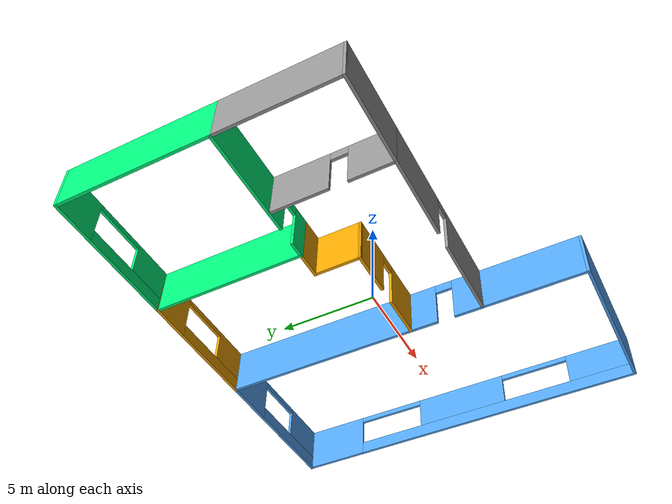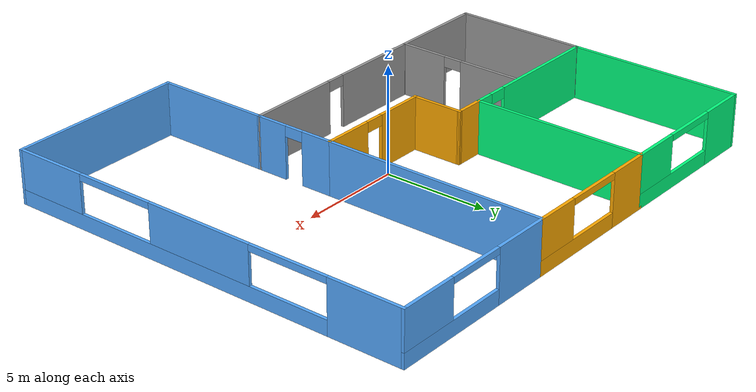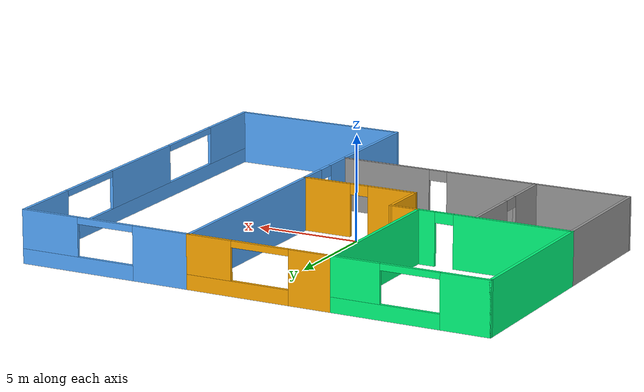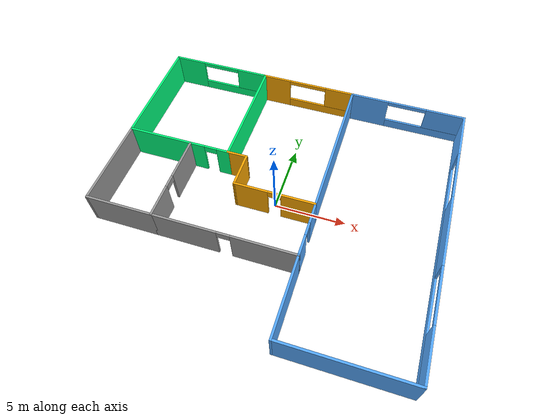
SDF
<?xml version='1.0'?>
<sdf version='1.6'>
  <model name='Building'>
    <link name='Wall_10'>
      <pose frame=''>2.99997 -7.175 0 0 -0 1.5708</pose>
      <self_collide>0</self_collide>
      <kinematic>0</kinematic>
      <visual name='Wall_10_Visual'>
        <pose frame=''>0 0 1.25 0 -0 0</pose>
        <geometry>
          <box>
            <size>5.5 0.15 2.5</size>
          </box>
        </geometry>
        <material>
          <script>
            <uri>file://media/materials/scripts/gazebo.material</uri>
            <name>Gazebo/Grey</name>
          </script>
          <ambient>0.333333 0.666667 1 1</ambient>
          <diffuse>0.7 0.7 0.7 1</diffuse>
          <specular>0.01 0.01 0.01 1</specular>
          <emissive>0 0 0 1</emissive>
        </material>
        <meta>
          <layer>0</layer>
        </meta>
        <transparency>0</transparency>
        <cast_shadows>1</cast_shadows>
      </visual>
      <collision name='Wall_10_Collision'>
        <laser_retro>0</laser_retro>
        <max_contacts>10</max_contacts>
        <pose frame=''>0 0 1.25 0 -0 0</pose>
        <geometry>
          <box>
            <size>5.5 0.15 2.5</size>
          </box>
        </geometry>
        <surface>
          <friction>
            <ode>
              <mu>1</mu>
              <mu2>1</mu2>
              <fdir1>0 0 0</fdir1>
              <slip1>0</slip1>
              <slip2>0</slip2>
            </ode>
            <torsional>
              <coefficient>1</coefficient>
              <patch_radius>0</patch_radius>
              <surface_radius>0</surface_radius>
              <use_patch_radius>1</use_patch_radius>
              <ode>
                <slip>0</slip>
              </ode>
            </torsional>
          </friction>
          <bounce>
            <restitution_coefficient>0</restitution_coefficient>
            <threshold>1e+06</threshold>
          </bounce>
          <contact>
            <collide_without_contact>0</collide_without_contact>
            <collide_without_contact_bitmask>1</collide_without_contact_bitmask>
            <collide_bitmask>1</collide_bitmask>
            <ode>
              <soft_cfm>0</soft_cfm>
              <soft_erp>0.2</soft_erp>
              <kp>1e+13</kp>
              <kd>1</kd>
              <max_vel>0.01</max_vel>
              <min_depth>0</min_depth>
            </ode>
            <bullet>
              <split_impulse>1</split_impulse>
              <split_impulse_penetration_threshold>-0.01</split_impulse_penetration_threshold>
              <soft_cfm>0</soft_cfm>
              <soft_erp>0.2</soft_erp>
              <kp>1e+13</kp>
              <kd>1</kd>
            </bullet>
          </contact>
        </surface>
      </collision>
    </link>
    <link name='Wall_48'>
      <pose frame=''>-6.77372 -1.40614 0 0 0 -1.5708</pose>
      <self_collide>0</self_collide>
      <kinematic>0</kinematic>
      <visual name='Wall_48_Visual_0'>
        <pose frame=''>-1.61017 0 1.25 0 -0 0</pose>
        <geometry>
          <box>
            <size>3.02966 0.15 2.5</size>
          </box>
        </geometry>
        <material>
          <script>
            <uri>file://media/materials/scripts/gazebo.material</uri>
            <name>Gazebo/Grey</name>
          </script>
          <ambient>1 1 1 1</ambient>
          <diffuse>0.7 0.7 0.7 1</diffuse>
          <specular>0.01 0.01 0.01 1</specular>
          <emissive>0 0 0 1</emissive>
        </material>
        <meta>
          <layer>0</layer>
        </meta>
        <transparency>0</transparency>
        <cast_shadows>1</cast_shadows>
      </visual>
      <visual name='Wall_48_Visual_1'>
        <pose frame=''>1.96483 0 1.25 0 -0 0</pose>
        <geometry>
          <box>
            <size>2.32034 0.15 2.5</size>
          </box>
        </geometry>
        <material>
          <script>
            <uri>file://media/materials/scripts/gazebo.material</uri>
            <name>Gazebo/Grey</name>
          </script>
          <ambient>1 1 1 1</ambient>
          <diffuse>0.7 0.7 0.7 1</diffuse>
          <specular>0.01 0.01 0.01 1</specular>
          <emissive>0 0 0 1</emissive>
        </material>
        <meta>
          <layer>0</layer>
        </meta>
        <transparency>0</transparency>
        <cast_shadows>1</cast_shadows>
      </visual>
      <visual name='Wall_48_Visual_2'>
        <pose frame=''>0.354659 0 2.25 0 -0 0</pose>
        <geometry>
          <box>
            <size>0.9 0.15 0.5</size>
          </box>
        </geometry>
        <material>
          <script>
            <uri>file://media/materials/scripts/gazebo.material</uri>
            <name>Gazebo/Grey</name>
          </script>
          <ambient>1 1 1 1</ambient>
          <diffuse>0.7 0.7 0.7 1</diffuse>
          <specular>0.01 0.01 0.01 1</specular>
          <emissive>0 0 0 1</emissive>
        </material>
        <meta>
          <layer>0</layer>
        </meta>
        <transparency>0</transparency>
        <cast_shadows>1</cast_shadows>
      </visual>
      <collision name='Wall_48_Collision_0'>
        <laser_retro>0</laser_retro>
        <max_contacts>10</max_contacts>
        <pose frame=''>-1.61017 0 1.25 0 -0 0</pose>
        <geometry>
          <box>
            <size>3.02966 0.15 2.5</size>
          </box>
        </geometry>
        <surface>
          <friction>
            <ode>
              <mu>1</mu>
              <mu2>1</mu2>
              <fdir1>0 0 0</fdir1>
              <slip1>0</slip1>
              <slip2>0</slip2>
            </ode>
            <torsional>
              <coefficient>1</coefficient>
              <patch_radius>0</patch_radius>
              <surface_radius>0</surface_radius>
              <use_patch_radius>1</use_patch_radius>
              <ode>
                <slip>0</slip>
              </ode>
            </torsional>
          </friction>
          <bounce>
            <restitution_coefficient>0</restitution_coefficient>
            <threshold>1e+06</threshold>
          </bounce>
          <contact>
            <collide_without_contact>0</collide_without_contact>
            <collide_without_contact_bitmask>1</collide_without_contact_bitmask>
            <collide_bitmask>1</collide_bitmask>
            <ode>
              <soft_cfm>0</soft_cfm>
              <soft_erp>0.2</soft_erp>
              <kp>1e+13</kp>
              <kd>1</kd>
              <max_vel>0.01</max_vel>
              <min_depth>0</min_depth>
            </ode>
            <bullet>
              <split_impulse>1</split_impulse>
              <split_impulse_penetration_threshold>-0.01</split_impulse_penetration_threshold>
              <soft_cfm>0</soft_cfm>
              <soft_erp>0.2</soft_erp>
              <kp>1e+13</kp>
              <kd>1</kd>
            </bullet>
          </contact>
        </surface>
      </collision>
      <collision name='Wall_48_Collision_1'>
        <laser_retro>0</laser_retro>
        <max_contacts>10</max_contacts>
        <pose frame=''>1.96483 0 1.25 0 -0 0</pose>
        <geometry>
          <box>
            <size>2.32034 0.15 2.5</size>
          </box>
        </geometry>
        <surface>
          <friction>
            <ode>
              <mu>1</mu>
              <mu2>1</mu2>
              <fdir1>0 0 0</fdir1>
              <slip1>0</slip1>
              <slip2>0</slip2>
            </ode>
            <torsional>
              <coefficient>1</coefficient>
              <patch_radius>0</patch_radius>
              <surface_radius>0</surface_radius>
              <use_patch_radius>1</use_patch_radius>
              <ode>
                <slip>0</slip>
              </ode>
            </torsional>
          </friction>
          <bounce>
            <restitution_coefficient>0</restitution_coefficient>
            <threshold>1e+06</threshold>
          </bounce>
          <contact>
            <collide_without_contact>0</collide_without_contact>
            <collide_without_contact_bitmask>1</collide_without_contact_bitmask>
            <collide_bitmask>1</collide_bitmask>
            <ode>
              <soft_cfm>0</soft_cfm>
              <soft_erp>0.2</soft_erp>
              <kp>1e+13</kp>
              <kd>1</kd>
              <max_vel>0.01</max_vel>
              <min_depth>0</min_depth>
            </ode>
            <bullet>
              <split_impulse>1</split_impulse>
              <split_impulse_penetration_threshold>-0.01</split_impulse_penetration_threshold>
              <soft_cfm>0</soft_cfm>
              <soft_erp>0.2</soft_erp>
              <kp>1e+13</kp>
              <kd>1</kd>
            </bullet>
          </contact>
        </surface>
      </collision>
      <collision name='Wall_48_Collision_2'>
        <laser_retro>0</laser_retro>
        <max_contacts>10</max_contacts>
        <pose frame=''>0.354659 0 2.25 0 -0 0</pose>
        <geometry>
          <box>
            <size>0.9 0.15 0.5</size>
          </box>
        </geometry>
        <surface>
          <friction>
            <ode>
              <mu>1</mu>
              <mu2>1</mu2>
              <fdir1>0 0 0</fdir1>
              <slip1>0</slip1>
              <slip2>0</slip2>
            </ode>
            <torsional>
              <coefficient>1</coefficient>
              <patch_radius>0</patch_radius>
              <surface_radius>0</surface_radius>
              <use_patch_radius>1</use_patch_radius>
              <ode>
                <slip>0</slip>
              </ode>
            </torsional>
          </friction>
          <bounce>
            <restitution_coefficient>0</restitution_coefficient>
            <threshold>1e+06</threshold>
          </bounce>
          <contact>
            <collide_without_contact>0</collide_without_contact>
            <collide_without_contact_bitmask>1</collide_without_contact_bitmask>
            <collide_bitmask>1</collide_bitmask>
            <ode>
              <soft_cfm>0</soft_cfm>
              <soft_erp>0.2</soft_erp>
              <kp>1e+13</kp>
              <kd>1</kd>
              <max_vel>0.01</max_vel>
              <min_depth>0</min_depth>
            </ode>
            <bullet>
              <split_impulse>1</split_impulse>
              <split_impulse_penetration_threshold>-0.01</split_impulse_penetration_threshold>
              <soft_cfm>0</soft_cfm>
              <soft_erp>0.2</soft_erp>
              <kp>1e+13</kp>
              <kd>1</kd>
            </bullet>
          </contact>
        </surface>
      </collision>
    </link>
    <link name='Wall_50'>
      <pose frame=''>-3.95628 5.78646 0 0 -0 1.5708</pose>
      <self_collide>0</self_collide>
      <kinematic>0</kinematic>
      <visual name='Wall_50_Visual'>
        <pose frame=''>0 0 1.25 0 -0 0</pose>
        <geometry>
          <box>
            <size>8.25 0.15 2.5</size>
          </box>
        </geometry>
        <material>
          <script>
            <uri>file://media/materials/scripts/gazebo.material</uri>
            <name>Gazebo/Grey</name>
          </script>
          <ambient>0 1 0.498039 1</ambient>
          <diffuse>0.7 0.7 0.7 1</diffuse>
          <specular>0.01 0.01 0.01 1</specular>
          <emissive>0 0 0 1</emissive>
        </material>
        <meta>
          <layer>0</layer>
        </meta>
        <transparency>0</transparency>
        <cast_shadows>1</cast_shadows>
      </visual>
      <collision name='Wall_50_Collision'>
        <laser_retro>0</laser_retro>
        <max_contacts>10</max_contacts>
        <pose frame=''>0 0 1.25 0 -0 0</pose>
        <geometry>
          <box>
            <size>8.25 0.15 2.5</size>
          </box>
        </geometry>
        <surface>
          <friction>
            <ode>
              <mu>1</mu>
              <mu2>1</mu2>
              <fdir1>0 0 0</fdir1>
              <slip1>0</slip1>
              <slip2>0</slip2>
            </ode>
            <torsional>
              <coefficient>1</coefficient>
              <patch_radius>0</patch_radius>
              <surface_radius>0</surface_radius>
              <use_patch_radius>1</use_patch_radius>
              <ode>
                <slip>0</slip>
              </ode>
            </torsional>
          </friction>
          <bounce>
            <restitution_coefficient>0</restitution_coefficient>
            <threshold>1e+06</threshold>
          </bounce>
          <contact>
            <collide_without_contact>0</collide_without_contact>
            <collide_without_contact_bitmask>1</collide_without_contact_bitmask>
            <collide_bitmask>1</collide_bitmask>
            <ode>
              <soft_cfm>0</soft_cfm>
              <soft_erp>0.2</soft_erp>
              <kp>1e+13</kp>
              <kd>1</kd>
              <max_vel>0.01</max_vel>
              <min_depth>0</min_depth>
            </ode>
            <bullet>
              <split_impulse>1</split_impulse>
              <split_impulse_penetration_threshold>-0.01</split_impulse_penetration_threshold>
              <soft_cfm>0</soft_cfm>
              <soft_erp>0.2</soft_erp>
              <kp>1e+13</kp>
              <kd>1</kd>
            </bullet>
          </contact>
        </surface>
      </collision>
    </link>
    <link name='Wall_53'>
      <pose frame=''>0.190752 -0.639237 0 0 -0 0</pose>
      <self_collide>0</self_collide>
      <kinematic>0</kinematic>
      <visual name='Wall_53_Visual_0'>
        <pose frame=''>-1.66349 0 1.25 0 -0 0</pose>
        <geometry>
          <box>
            <size>2.42302 0.15 2.5</size>
          </box>
        </geometry>
        <material>
          <script>
            <uri>file://media/materials/scripts/gazebo.material</uri>
            <name>Gazebo/Grey</name>
          </script>
          <ambient>1 0.666667 0 1</ambient>
          <diffuse>0.7 0.7 0.7 1</diffuse>
          <specular>0.01 0.01 0.01 1</specular>
          <emissive>0 0 0 1</emissive>
        </material>
        <meta>
          <layer>0</layer>
        </meta>
        <transparency>0</transparency>
        <cast_shadows>1</cast_shadows>
      </visual>
      <visual name='Wall_53_Visual_1'>
        <pose frame=''>1.66151 0 1.25 0 -0 0</pose>
        <geometry>
          <box>
            <size>2.42698 0.15 2.5</size>
          </box>
        </geometry>
        <material>
          <script>
            <uri>file://media/materials/scripts/gazebo.material</uri>
            <name>Gazebo/Grey</name>
          </script>
          <ambient>1 0.666667 0 1</ambient>
          <diffuse>0.7 0.7 0.7 1</diffuse>
          <specular>0.01 0.01 0.01 1</specular>
          <emissive>0 0 0 1</emissive>
        </material>
        <meta>
          <layer>0</layer>
        </meta>
        <transparency>0</transparency>
        <cast_shadows>1</cast_shadows>
      </visual>
      <visual name='Wall_53_Visual_2'>
        <pose frame=''>-0.001979 0 2.25 0 -0 0</pose>
        <geometry>
          <box>
            <size>0.9 0.15 0.5</size>
          </box>
        </geometry>
        <material>
          <script>
            <uri>file://media/materials/scripts/gazebo.material</uri>
            <name>Gazebo/Grey</name>
          </script>
          <ambient>1 0.666667 0 1</ambient>
          <diffuse>0.7 0.7 0.7 1</diffuse>
          <specular>0.01 0.01 0.01 1</specular>
          <emissive>0 0 0 1</emissive>
        </material>
        <meta>
          <layer>0</layer>
        </meta>
        <transparency>0</transparency>
        <cast_shadows>1</cast_shadows>
      </visual>
      <collision name='Wall_53_Collision_0'>
        <laser_retro>0</laser_retro>
        <max_contacts>10</max_contacts>
        <pose frame=''>-1.66349 0 1.25 0 -0 0</pose>
        <geometry>
          <box>
            <size>2.42302 0.15 2.5</size>
          </box>
        </geometry>
        <surface>
          <friction>
            <ode>
              <mu>1</mu>
              <mu2>1</mu2>
              <fdir1>0 0 0</fdir1>
              <slip1>0</slip1>
              <slip2>0</slip2>
            </ode>
            <torsional>
              <coefficient>1</coefficient>
              <patch_radius>0</patch_radius>
              <surface_radius>0</surface_radius>
              <use_patch_radius>1</use_patch_radius>
              <ode>
                <slip>0</slip>
              </ode>
            </torsional>
          </friction>
          <bounce>
            <restitution_coefficient>0</restitution_coefficient>
            <threshold>1e+06</threshold>
          </bounce>
          <contact>
            <collide_without_contact>0</collide_without_contact>
            <collide_without_contact_bitmask>1</collide_without_contact_bitmask>
            <collide_bitmask>1</collide_bitmask>
            <ode>
              <soft_cfm>0</soft_cfm>
              <soft_erp>0.2</soft_erp>
              <kp>1e+13</kp>
              <kd>1</kd>
              <max_vel>0.01</max_vel>
              <min_depth>0</min_depth>
            </ode>
            <bullet>
              <split_impulse>1</split_impulse>
              <split_impulse_penetration_threshold>-0.01</split_impulse_penetration_threshold>
              <soft_cfm>0</soft_cfm>
              <soft_erp>0.2</soft_erp>
              <kp>1e+13</kp>
              <kd>1</kd>
            </bullet>
          </contact>
        </surface>
      </collision>
      <collision name='Wall_53_Collision_1'>
        <laser_retro>0</laser_retro>
        <max_contacts>10</max_contacts>
        <pose frame=''>1.66151 0 1.25 0 -0 0</pose>
        <geometry>
          <box>
            <size>2.42698 0.15 2.5</size>
          </box>
        </geometry>
        <surface>
          <friction>
            <ode>
              <mu>1</mu>
              <mu2>1</mu2>
              <fdir1>0 0 0</fdir1>
              <slip1>0</slip1>
              <slip2>0</slip2>
            </ode>
            <torsional>
              <coefficient>1</coefficient>
              <patch_radius>0</patch_radius>
              <surface_radius>0</surface_radius>
              <use_patch_radius>1</use_patch_radius>
              <ode>
                <slip>0</slip>
              </ode>
            </torsional>
          </friction>
          <bounce>
            <restitution_coefficient>0</restitution_coefficient>
            <threshold>1e+06</threshold>
          </bounce>
          <contact>
            <collide_without_contact>0</collide_without_contact>
            <collide_without_contact_bitmask>1</collide_without_contact_bitmask>
            <collide_bitmask>1</collide_bitmask>
            <ode>
              <soft_cfm>0</soft_cfm>
              <soft_erp>0.2</soft_erp>
              <kp>1e+13</kp>
              <kd>1</kd>
              <max_vel>0.01</max_vel>
              <min_depth>0</min_depth>
            </ode>
            <bullet>
              <split_impulse>1</split_impulse>
              <split_impulse_penetration_threshold>-0.01</split_impulse_penetration_threshold>
              <soft_cfm>0</soft_cfm>
              <soft_erp>0.2</soft_erp>
              <kp>1e+13</kp>
              <kd>1</kd>
            </bullet>
          </contact>
        </surface>
      </collision>
      <collision name='Wall_53_Collision_2'>
        <laser_retro>0</laser_retro>
        <max_contacts>10</max_contacts>
        <pose frame=''>-0.001979 0 2.25 0 -0 0</pose>
        <geometry>
          <box>
            <size>0.9 0.15 0.5</size>
          </box>
        </geometry>
        <surface>
          <friction>
            <ode>
              <mu>1</mu>
              <mu2>1</mu2>
              <fdir1>0 0 0</fdir1>
              <slip1>0</slip1>
              <slip2>0</slip2>
            </ode>
            <torsional>
              <coefficient>1</coefficient>
              <patch_radius>0</patch_radius>
              <surface_radius>0</surface_radius>
              <use_patch_radius>1</use_patch_radius>
              <ode>
                <slip>0</slip>
              </ode>
            </torsional>
          </friction>
          <bounce>
            <restitution_coefficient>0</restitution_coefficient>
            <threshold>1e+06</threshold>
          </bounce>
          <contact>
            <collide_without_contact>0</collide_without_contact>
            <collide_without_contact_bitmask>1</collide_without_contact_bitmask>
            <collide_bitmask>1</collide_bitmask>
            <ode>
              <soft_cfm>0</soft_cfm>
              <soft_erp>0.2</soft_erp>
              <kp>1e+13</kp>
              <kd>1</kd>
              <max_vel>0.01</max_vel>
              <min_depth>0</min_depth>
            </ode>
            <bullet>
              <split_impulse>1</split_impulse>
              <split_impulse_penetration_threshold>-0.01</split_impulse_penetration_threshold>
              <soft_cfm>0</soft_cfm>
              <soft_erp>0.2</soft_erp>
              <kp>1e+13</kp>
              <kd>1</kd>
            </bullet>
          </contact>
        </surface>
      </collision>
    </link>
    <link name='Wall_56'>
      <pose frame=''>-3.28128 1.73646 0 0 -0 0</pose>
      <self_collide>0</self_collide>
      <kinematic>0</kinematic>
      <visual name='Wall_56_Visual'>
        <pose frame=''>0 0 1.25 0 -0 0</pose>
        <geometry>
          <box>
            <size>1.5 0.15 2.5</size>
          </box>
        </geometry>
        <material>
          <script>
            <uri>file://media/materials/scripts/gazebo.material</uri>
            <name>Gazebo/Grey</name>
          </script>
          <ambient>1 0.666667 0 1</ambient>
          <diffuse>0.7 0.7 0.7 1</diffuse>
          <specular>0.01 0.01 0.01 1</specular>
          <emissive>0 0 0 1</emissive>
        </material>
        <meta>
          <layer>0</layer>
        </meta>
        <transparency>0</transparency>
        <cast_shadows>1</cast_shadows>
      </visual>
      <collision name='Wall_56_Collision'>
        <laser_retro>0</laser_retro>
        <max_contacts>10</max_contacts>
        <pose frame=''>0 0 1.25 0 -0 0</pose>
        <geometry>
          <box>
            <size>1.5 0.15 2.5</size>
          </box>
        </geometry>
        <surface>
          <friction>
            <ode>
              <mu>1</mu>
              <mu2>1</mu2>
              <fdir1>0 0 0</fdir1>
              <slip1>0</slip1>
              <slip2>0</slip2>
            </ode>
            <torsional>
              <coefficient>1</coefficient>
              <patch_radius>0</patch_radius>
              <surface_radius>0</surface_radius>
              <use_patch_radius>1</use_patch_radius>
              <ode>
                <slip>0</slip>
              </ode>
            </torsional>
          </friction>
          <bounce>
            <restitution_coefficient>0</restitution_coefficient>
            <threshold>1e+06</threshold>
          </bounce>
          <contact>
            <collide_without_contact>0</collide_without_contact>
            <collide_without_contact_bitmask>1</collide_without_contact_bitmask>
            <collide_bitmask>1</collide_bitmask>
            <ode>
              <soft_cfm>0</soft_cfm>
              <soft_erp>0.2</soft_erp>
              <kp>1e+13</kp>
              <kd>1</kd>
              <max_vel>0.01</max_vel>
              <min_depth>0</min_depth>
            </ode>
            <bullet>
              <split_impulse>1</split_impulse>
              <split_impulse_penetration_threshold>-0.01</split_impulse_penetration_threshold>
              <soft_cfm>0</soft_cfm>
              <soft_erp>0.2</soft_erp>
              <kp>1e+13</kp>
              <kd>1</kd>
            </bullet>
          </contact>
        </surface>
      </collision>
    </link>
    <link name='Wall_57'>
      <pose frame=''>-2.60776 0.548611 0 0 0 -1.57205</pose>
      <self_collide>0</self_collide>
      <kinematic>0</kinematic>
      <visual name='Wall_57_Visual'>
        <pose frame=''>0 0 1.25 0 -0 0</pose>
        <geometry>
          <box>
            <size>2.5257 0.15 2.5</size>
          </box>
        </geometry>
        <material>
          <script>
            <uri>file://media/materials/scripts/gazebo.material</uri>
            <name>Gazebo/Grey</name>
          </script>
          <ambient>1 0.666667 0 1</ambient>
          <diffuse>0.7 0.7 0.7 1</diffuse>
          <specular>0.01 0.01 0.01 1</specular>
          <emissive>0 0 0 1</emissive>
        </material>
        <meta>
          <layer>0</layer>
        </meta>
        <transparency>0</transparency>
        <cast_shadows>1</cast_shadows>
      </visual>
      <collision name='Wall_57_Collision'>
        <laser_retro>0</laser_retro>
        <max_contacts>10</max_contacts>
        <pose frame=''>0 0 1.25 0 -0 0</pose>
        <geometry>
          <box>
            <size>2.5257 0.15 2.5</size>
          </box>
        </geometry>
        <surface>
          <friction>
            <ode>
              <mu>1</mu>
              <mu2>1</mu2>
              <fdir1>0 0 0</fdir1>
              <slip1>0</slip1>
              <slip2>0</slip2>
            </ode>
            <torsional>
              <coefficient>1</coefficient>
              <patch_radius>0</patch_radius>
              <surface_radius>0</surface_radius>
              <use_patch_radius>1</use_patch_radius>
              <ode>
                <slip>0</slip>
              </ode>
            </torsional>
          </friction>
          <bounce>
            <restitution_coefficient>0</restitution_coefficient>
            <threshold>1e+06</threshold>
          </bounce>
          <contact>
            <collide_without_contact>0</collide_without_contact>
            <collide_without_contact_bitmask>1</collide_without_contact_bitmask>
            <collide_bitmask>1</collide_bitmask>
            <ode>
              <soft_cfm>0</soft_cfm>
              <soft_erp>0.2</soft_erp>
              <kp>1e+13</kp>
              <kd>1</kd>
              <max_vel>0.01</max_vel>
              <min_depth>0</min_depth>
            </ode>
            <bullet>
              <split_impulse>1</split_impulse>
              <split_impulse_penetration_threshold>-0.01</split_impulse_penetration_threshold>
              <soft_cfm>0</soft_cfm>
              <soft_erp>0.2</soft_erp>
              <kp>1e+13</kp>
              <kd>1</kd>
            </bullet>
          </contact>
        </surface>
      </collision>
    </link>
    <link name='Wall_59'>
      <pose frame=''>-7.63128 1.73646 0 0 -0 3.14159</pose>
      <self_collide>0</self_collide>
      <kinematic>0</kinematic>
      <visual name='Wall_59_Visual_0'>
        <pose frame=''>-3.28588 0 1.25 0 -0 0</pose>
        <geometry>
          <box>
            <size>0.928242 0.15 2.5</size>
          </box>
        </geometry>
        <material>
          <script>
            <uri>file://media/materials/scripts/gazebo.material</uri>
            <name>Gazebo/Grey</name>
          </script>
          <ambient>0 1 0.498039 1</ambient>
          <diffuse>0.7 0.7 0.7 1</diffuse>
          <specular>0.01 0.01 0.01 1</specular>
          <emissive>0 0 0 1</emissive>
        </material>
        <meta>
          <layer>0</layer>
        </meta>
        <transparency>0</transparency>
        <cast_shadows>1</cast_shadows>
      </visual>
      <visual name='Wall_59_Visual_1'>
        <pose frame=''>0.914121 0 1.25 0 -0 0</pose>
        <geometry>
          <box>
            <size>5.67176 0.15 2.5</size>
          </box>
        </geometry>
        <material>
          <script>
            <uri>file://media/materials/scripts/gazebo.material</uri>
            <name>Gazebo/Grey</name>
          </script>
          <ambient>0 1 0.498039 1</ambient>
          <diffuse>0.7 0.7 0.7 1</diffuse>
          <specular>0.01 0.01 0.01 1</specular>
          <emissive>0 0 0 1</emissive>
        </material>
        <meta>
          <layer>0</layer>
        </meta>
        <transparency>0</transparency>
        <cast_shadows>1</cast_shadows>
      </visual>
      <visual name='Wall_59_Visual_2'>
        <pose frame=''>-2.37176 0 2.25 0 -0 0</pose>
        <geometry>
          <box>
            <size>0.9 0.15 0.5</size>
          </box>
        </geometry>
        <material>
          <script>
            <uri>file://media/materials/scripts/gazebo.material</uri>
            <name>Gazebo/Grey</name>
          </script>
          <ambient>0 1 0.498039 1</ambient>
          <diffuse>0.7 0.7 0.7 1</diffuse>
          <specular>0.01 0.01 0.01 1</specular>
          <emissive>0 0 0 1</emissive>
        </material>
        <meta>
          <layer>0</layer>
        </meta>
        <transparency>0</transparency>
        <cast_shadows>1</cast_shadows>
      </visual>
      <collision name='Wall_59_Collision_0'>
        <laser_retro>0</laser_retro>
        <max_contacts>10</max_contacts>
        <pose frame=''>-3.28588 0 1.25 0 -0 0</pose>
        <geometry>
          <box>
            <size>0.928242 0.15 2.5</size>
          </box>
        </geometry>
        <surface>
          <friction>
            <ode>
              <mu>1</mu>
              <mu2>1</mu2>
              <fdir1>0 0 0</fdir1>
              <slip1>0</slip1>
              <slip2>0</slip2>
            </ode>
            <torsional>
              <coefficient>1</coefficient>
              <patch_radius>0</patch_radius>
              <surface_radius>0</surface_radius>
              <use_patch_radius>1</use_patch_radius>
              <ode>
                <slip>0</slip>
              </ode>
            </torsional>
          </friction>
          <bounce>
            <restitution_coefficient>0</restitution_coefficient>
            <threshold>1e+06</threshold>
          </bounce>
          <contact>
            <collide_without_contact>0</collide_without_contact>
            <collide_without_contact_bitmask>1</collide_without_contact_bitmask>
            <collide_bitmask>1</collide_bitmask>
            <ode>
              <soft_cfm>0</soft_cfm>
              <soft_erp>0.2</soft_erp>
              <kp>1e+13</kp>
              <kd>1</kd>
              <max_vel>0.01</max_vel>
              <min_depth>0</min_depth>
            </ode>
            <bullet>
              <split_impulse>1</split_impulse>
              <split_impulse_penetration_threshold>-0.01</split_impulse_penetration_threshold>
              <soft_cfm>0</soft_cfm>
              <soft_erp>0.2</soft_erp>
              <kp>1e+13</kp>
              <kd>1</kd>
            </bullet>
          </contact>
        </surface>
      </collision>
      <collision name='Wall_59_Collision_1'>
        <laser_retro>0</laser_retro>
        <max_contacts>10</max_contacts>
        <pose frame=''>0.914121 0 1.25 0 -0 0</pose>
        <geometry>
          <box>
            <size>5.67176 0.15 2.5</size>
          </box>
        </geometry>
        <surface>
          <friction>
            <ode>
              <mu>1</mu>
              <mu2>1</mu2>
              <fdir1>0 0 0</fdir1>
              <slip1>0</slip1>
              <slip2>0</slip2>
            </ode>
            <torsional>
              <coefficient>1</coefficient>
              <patch_radius>0</patch_radius>
              <surface_radius>0</surface_radius>
              <use_patch_radius>1</use_patch_radius>
              <ode>
                <slip>0</slip>
              </ode>
            </torsional>
          </friction>
          <bounce>
            <restitution_coefficient>0</restitution_coefficient>
            <threshold>1e+06</threshold>
          </bounce>
          <contact>
            <collide_without_contact>0</collide_without_contact>
            <collide_without_contact_bitmask>1</collide_without_contact_bitmask>
            <collide_bitmask>1</collide_bitmask>
            <ode>
              <soft_cfm>0</soft_cfm>
              <soft_erp>0.2</soft_erp>
              <kp>1e+13</kp>
              <kd>1</kd>
              <max_vel>0.01</max_vel>
              <min_depth>0</min_depth>
            </ode>
            <bullet>
              <split_impulse>1</split_impulse>
              <split_impulse_penetration_threshold>-0.01</split_impulse_penetration_threshold>
              <soft_cfm>0</soft_cfm>
              <soft_erp>0.2</soft_erp>
              <kp>1e+13</kp>
              <kd>1</kd>
            </bullet>
          </contact>
        </surface>
      </collision>
      <collision name='Wall_59_Collision_2'>
        <laser_retro>0</laser_retro>
        <max_contacts>10</max_contacts>
        <pose frame=''>-2.37176 0 2.25 0 -0 0</pose>
        <geometry>
          <box>
            <size>0.9 0.15 0.5</size>
          </box>
        </geometry>
        <surface>
          <friction>
            <ode>
              <mu>1</mu>
              <mu2>1</mu2>
              <fdir1>0 0 0</fdir1>
              <slip1>0</slip1>
              <slip2>0</slip2>
            </ode>
            <torsional>
              <coefficient>1</coefficient>
              <patch_radius>0</patch_radius>
              <surface_radius>0</surface_radius>
              <use_patch_radius>1</use_patch_radius>
              <ode>
                <slip>0</slip>
              </ode>
            </torsional>
          </friction>
          <bounce>
            <restitution_coefficient>0</restitution_coefficient>
            <threshold>1e+06</threshold>
          </bounce>
          <contact>
            <collide_without_contact>0</collide_without_contact>
            <collide_without_contact_bitmask>1</collide_without_contact_bitmask>
            <collide_bitmask>1</collide_bitmask>
            <ode>
              <soft_cfm>0</soft_cfm>
              <soft_erp>0.2</soft_erp>
              <kp>1e+13</kp>
              <kd>1</kd>
              <max_vel>0.01</max_vel>
              <min_depth>0</min_depth>
            </ode>
            <bullet>
              <split_impulse>1</split_impulse>
              <split_impulse_penetration_threshold>-0.01</split_impulse_penetration_threshold>
              <soft_cfm>0</soft_cfm>
              <soft_erp>0.2</soft_erp>
              <kp>1e+13</kp>
              <kd>1</kd>
            </bullet>
          </contact>
        </surface>
      </collision>
    </link>
    <link name='Wall_63'>
      <pose frame=''>-7.67503 9.85 0 0 -0 0</pose>
      <self_collide>0</self_collide>
      <kinematic>0</kinematic>
      <visual name='Wall_63_Visual_0'>
        <pose frame=''>-2.57109 0 1.25 0 -0 0</pose>
        <geometry>
          <box>
            <size>2.35781 0.15 2.5</size>
          </box>
        </geometry>
        <material>
          <script>
            <uri>file://media/materials/scripts/gazebo.material</uri>
            <name>Gazebo/Grey</name>
          </script>
          <ambient>0 1 0.498039 1</ambient>
          <diffuse>0.7 0.7 0.7 1</diffuse>
          <specular>0.01 0.01 0.01 1</specular>
          <emissive>0 0 0 1</emissive>
        </material>
        <meta>
          <layer>0</layer>
        </meta>
        <transparency>0</transparency>
        <cast_shadows>1</cast_shadows>
      </visual>
      <visual name='Wall_63_Visual_1'>
        <pose frame=''>1.17891 0 0.35 0 -0 0</pose>
        <geometry>
          <box>
            <size>5.14219 0.15 0.7</size>
          </box>
        </geometry>
        <material>
          <script>
            <uri>file://media/materials/scripts/gazebo.material</uri>
            <name>Gazebo/Grey</name>
          </script>
          <ambient>0 1 0.498039 1</ambient>
          <diffuse>0.7 0.7 0.7 1</diffuse>
          <specular>0.01 0.01 0.01 1</specular>
          <emissive>0 0 0 1</emissive>
        </material>
        <meta>
          <layer>0</layer>
        </meta>
        <transparency>0</transparency>
        <cast_shadows>1</cast_shadows>
      </visual>
      <visual name='Wall_63_Visual_2'>
        <pose frame=''>2.57891 0 1.6 0 -0 0</pose>
        <geometry>
          <box>
            <size>2.34219 0.15 1.8</size>
          </box>
        </geometry>
        <material>
          <script>
            <uri>file://media/materials/scripts/gazebo.material</uri>
            <name>Gazebo/Grey</name>
          </script>
          <ambient>0 1 0.498039 1</ambient>
          <diffuse>0.7 0.7 0.7 1</diffuse>
          <specular>0.01 0.01 0.01 1</specular>
          <emissive>0 0 0 1</emissive>
        </material>
        <meta>
          <layer>0</layer>
        </meta>
        <transparency>0</transparency>
        <cast_shadows>1</cast_shadows>
      </visual>
      <visual name='Wall_63_Visual_3'>
        <pose frame=''>0.007813 0 2.35 0 -0 0</pose>
        <geometry>
          <box>
            <size>2.8 0.15 0.3</size>
          </box>
        </geometry>
        <material>
          <script>
            <uri>file://media/materials/scripts/gazebo.material</uri>
            <name>Gazebo/Grey</name>
          </script>
          <ambient>0 1 0.498039 1</ambient>
          <diffuse>0.7 0.7 0.7 1</diffuse>
          <specular>0.01 0.01 0.01 1</specular>
          <emissive>0 0 0 1</emissive>
        </material>
        <meta>
          <layer>0</layer>
        </meta>
        <transparency>0</transparency>
        <cast_shadows>1</cast_shadows>
      </visual>
      <collision name='Wall_63_Collision_0'>
        <laser_retro>0</laser_retro>
        <max_contacts>10</max_contacts>
        <pose frame=''>-2.57109 0 1.25 0 -0 0</pose>
        <geometry>
          <box>
            <size>2.35781 0.15 2.5</size>
          </box>
        </geometry>
        <surface>
          <friction>
            <ode>
              <mu>1</mu>
              <mu2>1</mu2>
              <fdir1>0 0 0</fdir1>
              <slip1>0</slip1>
              <slip2>0</slip2>
            </ode>
            <torsional>
              <coefficient>1</coefficient>
              <patch_radius>0</patch_radius>
              <surface_radius>0</surface_radius>
              <use_patch_radius>1</use_patch_radius>
              <ode>
                <slip>0</slip>
              </ode>
            </torsional>
          </friction>
          <bounce>
            <restitution_coefficient>0</restitution_coefficient>
            <threshold>1e+06</threshold>
          </bounce>
          <contact>
            <collide_without_contact>0</collide_without_contact>
            <collide_without_contact_bitmask>1</collide_without_contact_bitmask>
            <collide_bitmask>1</collide_bitmask>
            <ode>
              <soft_cfm>0</soft_cfm>
              <soft_erp>0.2</soft_erp>
              <kp>1e+13</kp>
              <kd>1</kd>
              <max_vel>0.01</max_vel>
              <min_depth>0</min_depth>
            </ode>
            <bullet>
              <split_impulse>1</split_impulse>
              <split_impulse_penetration_threshold>-0.01</split_impulse_penetration_threshold>
              <soft_cfm>0</soft_cfm>
              <soft_erp>0.2</soft_erp>
              <kp>1e+13</kp>
              <kd>1</kd>
            </bullet>
          </contact>
        </surface>
      </collision>
      <collision name='Wall_63_Collision_1'>
        <laser_retro>0</laser_retro>
        <max_contacts>10</max_contacts>
        <pose frame=''>1.17891 0 0.35 0 -0 0</pose>
        <geometry>
          <box>
            <size>5.14219 0.15 0.7</size>
          </box>
        </geometry>
        <surface>
          <friction>
            <ode>
              <mu>1</mu>
              <mu2>1</mu2>
              <fdir1>0 0 0</fdir1>
              <slip1>0</slip1>
              <slip2>0</slip2>
            </ode>
            <torsional>
              <coefficient>1</coefficient>
              <patch_radius>0</patch_radius>
              <surface_radius>0</surface_radius>
              <use_patch_radius>1</use_patch_radius>
              <ode>
                <slip>0</slip>
              </ode>
            </torsional>
          </friction>
          <bounce>
            <restitution_coefficient>0</restitution_coefficient>
            <threshold>1e+06</threshold>
          </bounce>
          <contact>
            <collide_without_contact>0</collide_without_contact>
            <collide_without_contact_bitmask>1</collide_without_contact_bitmask>
            <collide_bitmask>1</collide_bitmask>
            <ode>
              <soft_cfm>0</soft_cfm>
              <soft_erp>0.2</soft_erp>
              <kp>1e+13</kp>
              <kd>1</kd>
              <max_vel>0.01</max_vel>
              <min_depth>0</min_depth>
            </ode>
            <bullet>
              <split_impulse>1</split_impulse>
              <split_impulse_penetration_threshold>-0.01</split_impulse_penetration_threshold>
              <soft_cfm>0</soft_cfm>
              <soft_erp>0.2</soft_erp>
              <kp>1e+13</kp>
              <kd>1</kd>
            </bullet>
          </contact>
        </surface>
      </collision>
      <collision name='Wall_63_Collision_2'>
        <laser_retro>0</laser_retro>
        <max_contacts>10</max_contacts>
        <pose frame=''>2.57891 0 1.6 0 -0 0</pose>
        <geometry>
          <box>
            <size>2.34219 0.15 1.8</size>
          </box>
        </geometry>
        <surface>
          <friction>
            <ode>
              <mu>1</mu>
              <mu2>1</mu2>
              <fdir1>0 0 0</fdir1>
              <slip1>0</slip1>
              <slip2>0</slip2>
            </ode>
            <torsional>
              <coefficient>1</coefficient>
              <patch_radius>0</patch_radius>
              <surface_radius>0</surface_radius>
              <use_patch_radius>1</use_patch_radius>
              <ode>
                <slip>0</slip>
              </ode>
            </torsional>
          </friction>
          <bounce>
            <restitution_coefficient>0</restitution_coefficient>
            <threshold>1e+06</threshold>
          </bounce>
          <contact>
            <collide_without_contact>0</collide_without_contact>
            <collide_without_contact_bitmask>1</collide_without_contact_bitmask>
            <collide_bitmask>1</collide_bitmask>
            <ode>
              <soft_cfm>0</soft_cfm>
              <soft_erp>0.2</soft_erp>
              <kp>1e+13</kp>
              <kd>1</kd>
              <max_vel>0.01</max_vel>
              <min_depth>0</min_depth>
            </ode>
            <bullet>
              <split_impulse>1</split_impulse>
              <split_impulse_penetration_threshold>-0.01</split_impulse_penetration_threshold>
              <soft_cfm>0</soft_cfm>
              <soft_erp>0.2</soft_erp>
              <kp>1e+13</kp>
              <kd>1</kd>
            </bullet>
          </contact>
        </surface>
      </collision>
      <collision name='Wall_63_Collision_3'>
        <laser_retro>0</laser_retro>
        <max_contacts>10</max_contacts>
        <pose frame=''>0.007813 0 2.35 0 -0 0</pose>
        <geometry>
          <box>
            <size>2.8 0.15 0.3</size>
          </box>
        </geometry>
        <surface>
          <friction>
            <ode>
              <mu>1</mu>
              <mu2>1</mu2>
              <fdir1>0 0 0</fdir1>
              <slip1>0</slip1>
              <slip2>0</slip2>
            </ode>
            <torsional>
              <coefficient>1</coefficient>
              <patch_radius>0</patch_radius>
              <surface_radius>0</surface_radius>
              <use_patch_radius>1</use_patch_radius>
              <ode>
                <slip>0</slip>
              </ode>
            </torsional>
          </friction>
          <bounce>
            <restitution_coefficient>0</restitution_coefficient>
            <threshold>1e+06</threshold>
          </bounce>
          <contact>
            <collide_without_contact>0</collide_without_contact>
            <collide_without_contact_bitmask>1</collide_without_contact_bitmask>
            <collide_bitmask>1</collide_bitmask>
            <ode>
              <soft_cfm>0</soft_cfm>
              <soft_erp>0.2</soft_erp>
              <kp>1e+13</kp>
              <kd>1</kd>
              <max_vel>0.01</max_vel>
              <min_depth>0</min_depth>
            </ode>
            <bullet>
              <split_impulse>1</split_impulse>
              <split_impulse_penetration_threshold>-0.01</split_impulse_penetration_threshold>
              <soft_cfm>0</soft_cfm>
              <soft_erp>0.2</soft_erp>
              <kp>1e+13</kp>
              <kd>1</kd>
            </bullet>
          </contact>
        </surface>
      </collision>
    </link>
    <link name='Wall_64'>
      <pose frame=''>-0.500034 9.85 0 0 -0 0</pose>
      <self_collide>0</self_collide>
      <kinematic>0</kinematic>
      <visual name='Wall_64_Visual_0'>
        <pose frame=''>-2.49241 0 1.25 0 -0 0</pose>
        <geometry>
          <box>
            <size>2.16519 0.15 2.5</size>
          </box>
        </geometry>
        <material>
          <script>
            <uri>file://media/materials/scripts/gazebo.material</uri>
            <name>Gazebo/Grey</name>
          </script>
          <ambient>1 0.666667 0 1</ambient>
          <diffuse>0.7 0.7 0.7 1</diffuse>
          <specular>0.01 0.01 0.01 1</specular>
          <emissive>0 0 0 1</emissive>
        </material>
        <meta>
          <layer>0</layer>
        </meta>
        <transparency>0</transparency>
        <cast_shadows>1</cast_shadows>
      </visual>
      <visual name='Wall_64_Visual_1'>
        <pose frame=''>1.08259 0 0.35 0 -0 0</pose>
        <geometry>
          <box>
            <size>4.98481 0.15 0.7</size>
          </box>
        </geometry>
        <material>
          <script>
            <uri>file://media/materials/scripts/gazebo.material</uri>
            <name>Gazebo/Grey</name>
          </script>
          <ambient>1 0.666667 0 1</ambient>
          <diffuse>0.7 0.7 0.7 1</diffuse>
          <specular>0.01 0.01 0.01 1</specular>
          <emissive>0 0 0 1</emissive>
        </material>
        <meta>
          <layer>0</layer>
        </meta>
        <transparency>0</transparency>
        <cast_shadows>1</cast_shadows>
      </visual>
      <visual name='Wall_64_Visual_2'>
        <pose frame=''>2.48259 0 1.6 0 -0 0</pose>
        <geometry>
          <box>
            <size>2.18481 0.15 1.8</size>
          </box>
        </geometry>
        <material>
          <script>
            <uri>file://media/materials/scripts/gazebo.material</uri>
            <name>Gazebo/Grey</name>
          </script>
          <ambient>1 0.666667 0 1</ambient>
          <diffuse>0.7 0.7 0.7 1</diffuse>
          <specular>0.01 0.01 0.01 1</specular>
          <emissive>0 0 0 1</emissive>
        </material>
        <meta>
          <layer>0</layer>
        </meta>
        <transparency>0</transparency>
        <cast_shadows>1</cast_shadows>
      </visual>
      <visual name='Wall_64_Visual_3'>
        <pose frame=''>-0.009811 0 2.35 0 -0 0</pose>
        <geometry>
          <box>
            <size>2.8 0.15 0.3</size>
          </box>
        </geometry>
        <material>
          <script>
            <uri>file://media/materials/scripts/gazebo.material</uri>
            <name>Gazebo/Grey</name>
          </script>
          <ambient>1 0.666667 0 1</ambient>
          <diffuse>0.7 0.7 0.7 1</diffuse>
          <specular>0.01 0.01 0.01 1</specular>
          <emissive>0 0 0 1</emissive>
        </material>
        <meta>
          <layer>0</layer>
        </meta>
        <transparency>0</transparency>
        <cast_shadows>1</cast_shadows>
      </visual>
      <collision name='Wall_64_Collision_0'>
        <laser_retro>0</laser_retro>
        <max_contacts>10</max_contacts>
        <pose frame=''>-2.49241 0 1.25 0 -0 0</pose>
        <geometry>
          <box>
            <size>2.16519 0.15 2.5</size>
          </box>
        </geometry>
        <surface>
          <friction>
            <ode>
              <mu>1</mu>
              <mu2>1</mu2>
              <fdir1>0 0 0</fdir1>
              <slip1>0</slip1>
              <slip2>0</slip2>
            </ode>
            <torsional>
              <coefficient>1</coefficient>
              <patch_radius>0</patch_radius>
              <surface_radius>0</surface_radius>
              <use_patch_radius>1</use_patch_radius>
              <ode>
                <slip>0</slip>
              </ode>
            </torsional>
          </friction>
          <bounce>
            <restitution_coefficient>0</restitution_coefficient>
            <threshold>1e+06</threshold>
          </bounce>
          <contact>
            <collide_without_contact>0</collide_without_contact>
            <collide_without_contact_bitmask>1</collide_without_contact_bitmask>
            <collide_bitmask>1</collide_bitmask>
            <ode>
              <soft_cfm>0</soft_cfm>
              <soft_erp>0.2</soft_erp>
              <kp>1e+13</kp>
              <kd>1</kd>
              <max_vel>0.01</max_vel>
              <min_depth>0</min_depth>
            </ode>
            <bullet>
              <split_impulse>1</split_impulse>
              <split_impulse_penetration_threshold>-0.01</split_impulse_penetration_threshold>
              <soft_cfm>0</soft_cfm>
              <soft_erp>0.2</soft_erp>
              <kp>1e+13</kp>
              <kd>1</kd>
            </bullet>
          </contact>
        </surface>
      </collision>
      <collision name='Wall_64_Collision_1'>
        <laser_retro>0</laser_retro>
        <max_contacts>10</max_contacts>
        <pose frame=''>1.08259 0 0.35 0 -0 0</pose>
        <geometry>
          <box>
            <size>4.98481 0.15 0.7</size>
          </box>
        </geometry>
        <surface>
          <friction>
            <ode>
              <mu>1</mu>
              <mu2>1</mu2>
              <fdir1>0 0 0</fdir1>
              <slip1>0</slip1>
              <slip2>0</slip2>
            </ode>
            <torsional>
              <coefficient>1</coefficient>
              <patch_radius>0</patch_radius>
              <surface_radius>0</surface_radius>
              <use_patch_radius>1</use_patch_radius>
              <ode>
                <slip>0</slip>
              </ode>
            </torsional>
          </friction>
          <bounce>
            <restitution_coefficient>0</restitution_coefficient>
            <threshold>1e+06</threshold>
          </bounce>
          <contact>
            <collide_without_contact>0</collide_without_contact>
            <collide_without_contact_bitmask>1</collide_without_contact_bitmask>
            <collide_bitmask>1</collide_bitmask>
            <ode>
              <soft_cfm>0</soft_cfm>
              <soft_erp>0.2</soft_erp>
              <kp>1e+13</kp>
              <kd>1</kd>
              <max_vel>0.01</max_vel>
              <min_depth>0</min_depth>
            </ode>
            <bullet>
              <split_impulse>1</split_impulse>
              <split_impulse_penetration_threshold>-0.01</split_impulse_penetration_threshold>
              <soft_cfm>0</soft_cfm>
              <soft_erp>0.2</soft_erp>
              <kp>1e+13</kp>
              <kd>1</kd>
            </bullet>
          </contact>
        </surface>
      </collision>
      <collision name='Wall_64_Collision_2'>
        <laser_retro>0</laser_retro>
        <max_contacts>10</max_contacts>
        <pose frame=''>2.48259 0 1.6 0 -0 0</pose>
        <geometry>
          <box>
            <size>2.18481 0.15 1.8</size>
          </box>
        </geometry>
        <surface>
          <friction>
            <ode>
              <mu>1</mu>
              <mu2>1</mu2>
              <fdir1>0 0 0</fdir1>
              <slip1>0</slip1>
              <slip2>0</slip2>
            </ode>
            <torsional>
              <coefficient>1</coefficient>
              <patch_radius>0</patch_radius>
              <surface_radius>0</surface_radius>
              <use_patch_radius>1</use_patch_radius>
              <ode>
                <slip>0</slip>
              </ode>
            </torsional>
          </friction>
          <bounce>
            <restitution_coefficient>0</restitution_coefficient>
            <threshold>1e+06</threshold>
          </bounce>
          <contact>
            <collide_without_contact>0</collide_without_contact>
            <collide_without_contact_bitmask>1</collide_without_contact_bitmask>
            <collide_bitmask>1</collide_bitmask>
            <ode>
              <soft_cfm>0</soft_cfm>
              <soft_erp>0.2</soft_erp>
              <kp>1e+13</kp>
              <kd>1</kd>
              <max_vel>0.01</max_vel>
              <min_depth>0</min_depth>
            </ode>
            <bullet>
              <split_impulse>1</split_impulse>
              <split_impulse_penetration_threshold>-0.01</split_impulse_penetration_threshold>
              <soft_cfm>0</soft_cfm>
              <soft_erp>0.2</soft_erp>
              <kp>1e+13</kp>
              <kd>1</kd>
            </bullet>
          </contact>
        </surface>
      </collision>
      <collision name='Wall_64_Collision_3'>
        <laser_retro>0</laser_retro>
        <max_contacts>10</max_contacts>
        <pose frame=''>-0.009811 0 2.35 0 -0 0</pose>
        <geometry>
          <box>
            <size>2.8 0.15 0.3</size>
          </box>
        </geometry>
        <surface>
          <friction>
            <ode>
              <mu>1</mu>
              <mu2>1</mu2>
              <fdir1>0 0 0</fdir1>
              <slip1>0</slip1>
              <slip2>0</slip2>
            </ode>
            <torsional>
              <coefficient>1</coefficient>
              <patch_radius>0</patch_radius>
              <surface_radius>0</surface_radius>
              <use_patch_radius>1</use_patch_radius>
              <ode>
                <slip>0</slip>
              </ode>
            </torsional>
          </friction>
          <bounce>
            <restitution_coefficient>0</restitution_coefficient>
            <threshold>1e+06</threshold>
          </bounce>
          <contact>
            <collide_without_contact>0</collide_without_contact>
            <collide_without_contact_bitmask>1</collide_without_contact_bitmask>
            <collide_bitmask>1</collide_bitmask>
            <ode>
              <soft_cfm>0</soft_cfm>
              <soft_erp>0.2</soft_erp>
              <kp>1e+13</kp>
              <kd>1</kd>
              <max_vel>0.01</max_vel>
              <min_depth>0</min_depth>
            </ode>
            <bullet>
              <split_impulse>1</split_impulse>
              <split_impulse_penetration_threshold>-0.01</split_impulse_penetration_threshold>
              <soft_cfm>0</soft_cfm>
              <soft_erp>0.2</soft_erp>
              <kp>1e+13</kp>
              <kd>1</kd>
            </bullet>
          </contact>
        </surface>
      </collision>
    </link>
    <link name='Wall_65'>
      <pose frame=''>7.175 9.84997 0 0 0 -7e-06</pose>
      <self_collide>0</self_collide>
      <kinematic>0</kinematic>
      <visual name='Wall_65_Visual_0'>
        <pose frame=''>-2.82562 0 1.25 0 -0 0</pose>
        <geometry>
          <box>
            <size>2.84883 0.15 2.5</size>
          </box>
        </geometry>
        <material>
          <script>
            <uri>file://media/materials/scripts/gazebo.material</uri>
            <name>Gazebo/Grey</name>
          </script>
          <ambient>0.333333 0.666667 1 1</ambient>
          <diffuse>0.7 0.7 0.7 1</diffuse>
          <specular>0.01 0.01 0.01 1</specular>
          <emissive>0 0 0 1</emissive>
        </material>
        <meta>
          <layer>0</layer>
        </meta>
        <transparency>0</transparency>
        <cast_shadows>1</cast_shadows>
      </visual>
      <visual name='Wall_65_Visual_1'>
        <pose frame=''>1.42442 0 0.35 0 -0 0</pose>
        <geometry>
          <box>
            <size>5.65124 0.15 0.7</size>
          </box>
        </geometry>
        <material>
          <script>
            <uri>file://media/materials/scripts/gazebo.material</uri>
            <name>Gazebo/Grey</name>
          </script>
          <ambient>0.333333 0.666667 1 1</ambient>
          <diffuse>0.7 0.7 0.7 1</diffuse>
          <specular>0.01 0.01 0.01 1</specular>
          <emissive>0 0 0 1</emissive>
        </material>
        <meta>
          <layer>0</layer>
        </meta>
        <transparency>0</transparency>
        <cast_shadows>1</cast_shadows>
      </visual>
      <visual name='Wall_65_Visual_2'>
        <pose frame=''>2.82442 0 1.6 0 -0 0</pose>
        <geometry>
          <box>
            <size>2.85124 0.15 1.8</size>
          </box>
        </geometry>
        <material>
          <script>
            <uri>file://media/materials/scripts/gazebo.material</uri>
            <name>Gazebo/Grey</name>
          </script>
          <ambient>0.333333 0.666667 1 1</ambient>
          <diffuse>0.7 0.7 0.7 1</diffuse>
          <specular>0.01 0.01 0.01 1</specular>
          <emissive>0 0 0 1</emissive>
        </material>
        <meta>
          <layer>0</layer>
        </meta>
        <transparency>0</transparency>
        <cast_shadows>1</cast_shadows>
      </visual>
      <visual name='Wall_65_Visual_3'>
        <pose frame=''>-0.001203 0 2.35 0 -0 0</pose>
        <geometry>
          <box>
            <size>2.8 0.15 0.3</size>
          </box>
        </geometry>
        <material>
          <script>
            <uri>file://media/materials/scripts/gazebo.material</uri>
            <name>Gazebo/Grey</name>
          </script>
          <ambient>0.333333 0.666667 1 1</ambient>
          <diffuse>0.7 0.7 0.7 1</diffuse>
          <specular>0.01 0.01 0.01 1</specular>
          <emissive>0 0 0 1</emissive>
        </material>
        <meta>
          <layer>0</layer>
        </meta>
        <transparency>0</transparency>
        <cast_shadows>1</cast_shadows>
      </visual>
      <collision name='Wall_65_Collision_0'>
        <laser_retro>0</laser_retro>
        <max_contacts>10</max_contacts>
        <pose frame=''>-2.82562 0 1.25 0 -0 0</pose>
        <geometry>
          <box>
            <size>2.84883 0.15 2.5</size>
          </box>
        </geometry>
        <surface>
          <friction>
            <ode>
              <mu>1</mu>
              <mu2>1</mu2>
              <fdir1>0 0 0</fdir1>
              <slip1>0</slip1>
              <slip2>0</slip2>
            </ode>
            <torsional>
              <coefficient>1</coefficient>
              <patch_radius>0</patch_radius>
              <surface_radius>0</surface_radius>
              <use_patch_radius>1</use_patch_radius>
              <ode>
                <slip>0</slip>
              </ode>
            </torsional>
          </friction>
          <bounce>
            <restitution_coefficient>0</restitution_coefficient>
            <threshold>1e+06</threshold>
          </bounce>
          <contact>
            <collide_without_contact>0</collide_without_contact>
            <collide_without_contact_bitmask>1</collide_without_contact_bitmask>
            <collide_bitmask>1</collide_bitmask>
            <ode>
              <soft_cfm>0</soft_cfm>
              <soft_erp>0.2</soft_erp>
              <kp>1e+13</kp>
              <kd>1</kd>
              <max_vel>0.01</max_vel>
              <min_depth>0</min_depth>
            </ode>
            <bullet>
              <split_impulse>1</split_impulse>
              <split_impulse_penetration_threshold>-0.01</split_impulse_penetration_threshold>
              <soft_cfm>0</soft_cfm>
              <soft_erp>0.2</soft_erp>
              <kp>1e+13</kp>
              <kd>1</kd>
            </bullet>
          </contact>
        </surface>
      </collision>
      <collision name='Wall_65_Collision_1'>
        <laser_retro>0</laser_retro>
        <max_contacts>10</max_contacts>
        <pose frame=''>1.42442 0 0.35 0 -0 0</pose>
        <geometry>
          <box>
            <size>5.65124 0.15 0.7</size>
          </box>
        </geometry>
        <surface>
          <friction>
            <ode>
              <mu>1</mu>
              <mu2>1</mu2>
              <fdir1>0 0 0</fdir1>
              <slip1>0</slip1>
              <slip2>0</slip2>
            </ode>
            <torsional>
              <coefficient>1</coefficient>
              <patch_radius>0</patch_radius>
              <surface_radius>0</surface_radius>
              <use_patch_radius>1</use_patch_radius>
              <ode>
                <slip>0</slip>
              </ode>
            </torsional>
          </friction>
          <bounce>
            <restitution_coefficient>0</restitution_coefficient>
            <threshold>1e+06</threshold>
          </bounce>
          <contact>
            <collide_without_contact>0</collide_without_contact>
            <collide_without_contact_bitmask>1</collide_without_contact_bitmask>
            <collide_bitmask>1</collide_bitmask>
            <ode>
              <soft_cfm>0</soft_cfm>
              <soft_erp>0.2</soft_erp>
              <kp>1e+13</kp>
              <kd>1</kd>
              <max_vel>0.01</max_vel>
              <min_depth>0</min_depth>
            </ode>
            <bullet>
              <split_impulse>1</split_impulse>
              <split_impulse_penetration_threshold>-0.01</split_impulse_penetration_threshold>
              <soft_cfm>0</soft_cfm>
              <soft_erp>0.2</soft_erp>
              <kp>1e+13</kp>
              <kd>1</kd>
            </bullet>
          </contact>
        </surface>
      </collision>
      <collision name='Wall_65_Collision_2'>
        <laser_retro>0</laser_retro>
        <max_contacts>10</max_contacts>
        <pose frame=''>2.82442 0 1.6 0 -0 0</pose>
        <geometry>
          <box>
            <size>2.85124 0.15 1.8</size>
          </box>
        </geometry>
        <surface>
          <friction>
            <ode>
              <mu>1</mu>
              <mu2>1</mu2>
              <fdir1>0 0 0</fdir1>
              <slip1>0</slip1>
              <slip2>0</slip2>
            </ode>
            <torsional>
              <coefficient>1</coefficient>
              <patch_radius>0</patch_radius>
              <surface_radius>0</surface_radius>
              <use_patch_radius>1</use_patch_radius>
              <ode>
                <slip>0</slip>
              </ode>
            </torsional>
          </friction>
          <bounce>
            <restitution_coefficient>0</restitution_coefficient>
            <threshold>1e+06</threshold>
          </bounce>
          <contact>
            <collide_without_contact>0</collide_without_contact>
            <collide_without_contact_bitmask>1</collide_without_contact_bitmask>
            <collide_bitmask>1</collide_bitmask>
            <ode>
              <soft_cfm>0</soft_cfm>
              <soft_erp>0.2</soft_erp>
              <kp>1e+13</kp>
              <kd>1</kd>
              <max_vel>0.01</max_vel>
              <min_depth>0</min_depth>
            </ode>
            <bullet>
              <split_impulse>1</split_impulse>
              <split_impulse_penetration_threshold>-0.01</split_impulse_penetration_threshold>
              <soft_cfm>0</soft_cfm>
              <soft_erp>0.2</soft_erp>
              <kp>1e+13</kp>
              <kd>1</kd>
            </bullet>
          </contact>
        </surface>
      </collision>
      <collision name='Wall_65_Collision_3'>
        <laser_retro>0</laser_retro>
        <max_contacts>10</max_contacts>
        <pose frame=''>-0.001203 0 2.35 0 -0 0</pose>
        <geometry>
          <box>
            <size>2.8 0.15 0.3</size>
          </box>
        </geometry>
        <surface>
          <friction>
            <ode>
              <mu>1</mu>
              <mu2>1</mu2>
              <fdir1>0 0 0</fdir1>
              <slip1>0</slip1>
              <slip2>0</slip2>
            </ode>
            <torsional>
              <coefficient>1</coefficient>
              <patch_radius>0</patch_radius>
              <surface_radius>0</surface_radius>
              <use_patch_radius>1</use_patch_radius>
              <ode>
                <slip>0</slip>
              </ode>
            </torsional>
          </friction>
          <bounce>
            <restitution_coefficient>0</restitution_coefficient>
            <threshold>1e+06</threshold>
          </bounce>
          <contact>
            <collide_without_contact>0</collide_without_contact>
            <collide_without_contact_bitmask>1</collide_without_contact_bitmask>
            <collide_bitmask>1</collide_bitmask>
            <ode>
              <soft_cfm>0</soft_cfm>
              <soft_erp>0.2</soft_erp>
              <kp>1e+13</kp>
              <kd>1</kd>
              <max_vel>0.01</max_vel>
              <min_depth>0</min_depth>
            </ode>
            <bullet>
              <split_impulse>1</split_impulse>
              <split_impulse_penetration_threshold>-0.01</split_impulse_penetration_threshold>
              <soft_cfm>0</soft_cfm>
              <soft_erp>0.2</soft_erp>
              <kp>1e+13</kp>
              <kd>1</kd>
            </bullet>
          </contact>
        </surface>
      </collision>
    </link>
    <link name='Wall_67'>
      <pose frame=''>-11.35 5.8 0 0 0 -1.5708</pose>
      <self_collide>0</self_collide>
      <kinematic>0</kinematic>
      <visual name='Wall_67_Visual'>
        <pose frame=''>0 0 1.25 0 -0 0</pose>
        <geometry>
          <box>
            <size>8.25 0.15 2.5</size>
          </box>
        </geometry>
        <material>
          <script>
            <uri>file://media/materials/scripts/gazebo.material</uri>
            <name>Gazebo/Grey</name>
          </script>
          <ambient>0 1 0.498039 1</ambient>
          <diffuse>0.7 0.7 0.7 1</diffuse>
          <specular>0.01 0.01 0.01 1</specular>
          <emissive>0 0 0 1</emissive>
        </material>
        <meta>
          <layer>0</layer>
        </meta>
        <transparency>0</transparency>
        <cast_shadows>1</cast_shadows>
      </visual>
      <collision name='Wall_67_Collision'>
        <laser_retro>0</laser_retro>
        <max_contacts>10</max_contacts>
        <pose frame=''>0 0 1.25 0 -0 0</pose>
        <geometry>
          <box>
            <size>8.25 0.15 2.5</size>
          </box>
        </geometry>
        <surface>
          <friction>
            <ode>
              <mu>1</mu>
              <mu2>1</mu2>
              <fdir1>0 0 0</fdir1>
              <slip1>0</slip1>
              <slip2>0</slip2>
            </ode>
            <torsional>
              <coefficient>1</coefficient>
              <patch_radius>0</patch_radius>
              <surface_radius>0</surface_radius>
              <use_patch_radius>1</use_patch_radius>
              <ode>
                <slip>0</slip>
              </ode>
            </torsional>
          </friction>
          <bounce>
            <restitution_coefficient>0</restitution_coefficient>
            <threshold>1e+06</threshold>
          </bounce>
          <contact>
            <collide_without_contact>0</collide_without_contact>
            <collide_without_contact_bitmask>1</collide_without_contact_bitmask>
            <collide_bitmask>1</collide_bitmask>
            <ode>
              <soft_cfm>0</soft_cfm>
              <soft_erp>0.2</soft_erp>
              <kp>1e+13</kp>
              <kd>1</kd>
              <max_vel>0.01</max_vel>
              <min_depth>0</min_depth>
            </ode>
            <bullet>
              <split_impulse>1</split_impulse>
              <split_impulse_penetration_threshold>-0.01</split_impulse_penetration_threshold>
              <soft_cfm>0</soft_cfm>
              <soft_erp>0.2</soft_erp>
              <kp>1e+13</kp>
              <kd>1</kd>
            </bullet>
          </contact>
        </surface>
      </collision>
    </link>
    <link name='Wall_68'>
      <pose frame=''>-11.35 -1.375 0 0 0 -1.5708</pose>
      <self_collide>0</self_collide>
      <kinematic>0</kinematic>
      <visual name='Wall_68_Visual'>
        <pose frame=''>0 0 1.25 0 -0 0</pose>
        <geometry>
          <box>
            <size>6.4 0.15 2.5</size>
          </box>
        </geometry>
        <material>
          <script>
            <uri>file://media/materials/scripts/gazebo.material</uri>
            <name>Gazebo/Grey</name>
          </script>
          <ambient>1 1 1 1</ambient>
          <diffuse>0.7 0.7 0.7 1</diffuse>
          <specular>0.01 0.01 0.01 1</specular>
          <emissive>0 0 0 1</emissive>
        </material>
        <meta>
          <layer>0</layer>
        </meta>
        <transparency>0</transparency>
        <cast_shadows>1</cast_shadows>
      </visual>
      <collision name='Wall_68_Collision'>
        <laser_retro>0</laser_retro>
        <max_contacts>10</max_contacts>
        <pose frame=''>0 0 1.25 0 -0 0</pose>
        <geometry>
          <box>
            <size>6.4 0.15 2.5</size>
          </box>
        </geometry>
        <surface>
          <friction>
            <ode>
              <mu>1</mu>
              <mu2>1</mu2>
              <fdir1>0 0 0</fdir1>
              <slip1>0</slip1>
              <slip2>0</slip2>
            </ode>
            <torsional>
              <coefficient>1</coefficient>
              <patch_radius>0</patch_radius>
              <surface_radius>0</surface_radius>
              <use_patch_radius>1</use_patch_radius>
              <ode>
                <slip>0</slip>
              </ode>
            </torsional>
          </friction>
          <bounce>
            <restitution_coefficient>0</restitution_coefficient>
            <threshold>1e+06</threshold>
          </bounce>
          <contact>
            <collide_without_contact>0</collide_without_contact>
            <collide_without_contact_bitmask>1</collide_without_contact_bitmask>
            <collide_bitmask>1</collide_bitmask>
            <ode>
              <soft_cfm>0</soft_cfm>
              <soft_erp>0.2</soft_erp>
              <kp>1e+13</kp>
              <kd>1</kd>
              <max_vel>0.01</max_vel>
              <min_depth>0</min_depth>
            </ode>
            <bullet>
              <split_impulse>1</split_impulse>
              <split_impulse_penetration_threshold>-0.01</split_impulse_penetration_threshold>
              <soft_cfm>0</soft_cfm>
              <soft_erp>0.2</soft_erp>
              <kp>1e+13</kp>
              <kd>1</kd>
            </bullet>
          </contact>
        </surface>
      </collision>
    </link>
    <link name='Wall_70'>
      <pose frame=''>-9.05003 -4.5 0 0 -0 0</pose>
      <self_collide>0</self_collide>
      <kinematic>0</kinematic>
      <visual name='Wall_70_Visual'>
        <pose frame=''>0 0 1.25 0 -0 0</pose>
        <geometry>
          <box>
            <size>4.75 0.15 2.5</size>
          </box>
        </geometry>
        <material>
          <script>
            <uri>file://media/materials/scripts/gazebo.material</uri>
            <name>Gazebo/Grey</name>
          </script>
          <ambient>1 1 1 1</ambient>
          <diffuse>0.7 0.7 0.7 1</diffuse>
          <specular>0.01 0.01 0.01 1</specular>
          <emissive>0 0 0 1</emissive>
        </material>
        <meta>
          <layer>0</layer>
        </meta>
        <transparency>0</transparency>
        <cast_shadows>1</cast_shadows>
      </visual>
      <collision name='Wall_70_Collision'>
        <laser_retro>0</laser_retro>
        <max_contacts>10</max_contacts>
        <pose frame=''>0 0 1.25 0 -0 0</pose>
        <geometry>
          <box>
            <size>4.75 0.15 2.5</size>
          </box>
        </geometry>
        <surface>
          <friction>
            <ode>
              <mu>1</mu>
              <mu2>1</mu2>
              <fdir1>0 0 0</fdir1>
              <slip1>0</slip1>
              <slip2>0</slip2>
            </ode>
            <torsional>
              <coefficient>1</coefficient>
              <patch_radius>0</patch_radius>
              <surface_radius>0</surface_radius>
              <use_patch_radius>1</use_patch_radius>
              <ode>
                <slip>0</slip>
              </ode>
            </torsional>
          </friction>
          <bounce>
            <restitution_coefficient>0</restitution_coefficient>
            <threshold>1e+06</threshold>
          </bounce>
          <contact>
            <collide_without_contact>0</collide_without_contact>
            <collide_without_contact_bitmask>1</collide_without_contact_bitmask>
            <collide_bitmask>1</collide_bitmask>
            <ode>
              <soft_cfm>0</soft_cfm>
              <soft_erp>0.2</soft_erp>
              <kp>1e+13</kp>
              <kd>1</kd>
              <max_vel>0.01</max_vel>
              <min_depth>0</min_depth>
            </ode>
            <bullet>
              <split_impulse>1</split_impulse>
              <split_impulse_penetration_threshold>-0.01</split_impulse_penetration_threshold>
              <soft_cfm>0</soft_cfm>
              <soft_erp>0.2</soft_erp>
              <kp>1e+13</kp>
              <kd>1</kd>
            </bullet>
          </contact>
        </surface>
      </collision>
    </link>
    <link name='Wall_71'>
      <pose frame=''>-1.87503 -4.5 0 0 -0 0</pose>
      <self_collide>0</self_collide>
      <kinematic>0</kinematic>
      <visual name='Wall_71_Visual_0'>
        <pose frame=''>-2.70254 0 1.25 0 -0 0</pose>
        <geometry>
          <box>
            <size>4.49493 0.15 2.5</size>
          </box>
        </geometry>
        <material>
          <script>
            <uri>file://media/materials/scripts/gazebo.material</uri>
            <name>Gazebo/Grey</name>
          </script>
          <ambient>1 1 1 1</ambient>
          <diffuse>0.7 0.7 0.7 1</diffuse>
          <specular>0.01 0.01 0.01 1</specular>
          <emissive>0 0 0 1</emissive>
        </material>
        <meta>
          <layer>0</layer>
        </meta>
        <transparency>0</transparency>
        <cast_shadows>1</cast_shadows>
      </visual>
      <visual name='Wall_71_Visual_1'>
        <pose frame=''>2.69746 0 1.25 0 -0 0</pose>
        <geometry>
          <box>
            <size>4.50507 0.15 2.5</size>
          </box>
        </geometry>
        <material>
          <script>
            <uri>file://media/materials/scripts/gazebo.material</uri>
            <name>Gazebo/Grey</name>
          </script>
          <ambient>1 1 1 1</ambient>
          <diffuse>0.7 0.7 0.7 1</diffuse>
          <specular>0.01 0.01 0.01 1</specular>
          <emissive>0 0 0 1</emissive>
        </material>
        <meta>
          <layer>0</layer>
        </meta>
        <transparency>0</transparency>
        <cast_shadows>1</cast_shadows>
      </visual>
      <visual name='Wall_71_Visual_2'>
        <pose frame=''>-0.005072 0 2.25 0 -0 0</pose>
        <geometry>
          <box>
            <size>0.9 0.15 0.5</size>
          </box>
        </geometry>
        <material>
          <script>
            <uri>file://media/materials/scripts/gazebo.material</uri>
            <name>Gazebo/Grey</name>
          </script>
          <ambient>1 1 1 1</ambient>
          <diffuse>0.7 0.7 0.7 1</diffuse>
          <specular>0.01 0.01 0.01 1</specular>
          <emissive>0 0 0 1</emissive>
        </material>
        <meta>
          <layer>0</layer>
        </meta>
        <transparency>0</transparency>
        <cast_shadows>1</cast_shadows>
      </visual>
      <collision name='Wall_71_Collision_0'>
        <laser_retro>0</laser_retro>
        <max_contacts>10</max_contacts>
        <pose frame=''>-2.70254 0 1.25 0 -0 0</pose>
        <geometry>
          <box>
            <size>4.49493 0.15 2.5</size>
          </box>
        </geometry>
        <surface>
          <friction>
            <ode>
              <mu>1</mu>
              <mu2>1</mu2>
              <fdir1>0 0 0</fdir1>
              <slip1>0</slip1>
              <slip2>0</slip2>
            </ode>
            <torsional>
              <coefficient>1</coefficient>
              <patch_radius>0</patch_radius>
              <surface_radius>0</surface_radius>
              <use_patch_radius>1</use_patch_radius>
              <ode>
                <slip>0</slip>
              </ode>
            </torsional>
          </friction>
          <bounce>
            <restitution_coefficient>0</restitution_coefficient>
            <threshold>1e+06</threshold>
          </bounce>
          <contact>
            <collide_without_contact>0</collide_without_contact>
            <collide_without_contact_bitmask>1</collide_without_contact_bitmask>
            <collide_bitmask>1</collide_bitmask>
            <ode>
              <soft_cfm>0</soft_cfm>
              <soft_erp>0.2</soft_erp>
              <kp>1e+13</kp>
              <kd>1</kd>
              <max_vel>0.01</max_vel>
              <min_depth>0</min_depth>
            </ode>
            <bullet>
              <split_impulse>1</split_impulse>
              <split_impulse_penetration_threshold>-0.01</split_impulse_penetration_threshold>
              <soft_cfm>0</soft_cfm>
              <soft_erp>0.2</soft_erp>
              <kp>1e+13</kp>
              <kd>1</kd>
            </bullet>
          </contact>
        </surface>
      </collision>
      <collision name='Wall_71_Collision_1'>
        <laser_retro>0</laser_retro>
        <max_contacts>10</max_contacts>
        <pose frame=''>2.69746 0 1.25 0 -0 0</pose>
        <geometry>
          <box>
            <size>4.50507 0.15 2.5</size>
          </box>
        </geometry>
        <surface>
          <friction>
            <ode>
              <mu>1</mu>
              <mu2>1</mu2>
              <fdir1>0 0 0</fdir1>
              <slip1>0</slip1>
              <slip2>0</slip2>
            </ode>
            <torsional>
              <coefficient>1</coefficient>
              <patch_radius>0</patch_radius>
              <surface_radius>0</surface_radius>
              <use_patch_radius>1</use_patch_radius>
              <ode>
                <slip>0</slip>
              </ode>
            </torsional>
          </friction>
          <bounce>
            <restitution_coefficient>0</restitution_coefficient>
            <threshold>1e+06</threshold>
          </bounce>
          <contact>
            <collide_without_contact>0</collide_without_contact>
            <collide_without_contact_bitmask>1</collide_without_contact_bitmask>
            <collide_bitmask>1</collide_bitmask>
            <ode>
              <soft_cfm>0</soft_cfm>
              <soft_erp>0.2</soft_erp>
              <kp>1e+13</kp>
              <kd>1</kd>
              <max_vel>0.01</max_vel>
              <min_depth>0</min_depth>
            </ode>
            <bullet>
              <split_impulse>1</split_impulse>
              <split_impulse_penetration_threshold>-0.01</split_impulse_penetration_threshold>
              <soft_cfm>0</soft_cfm>
              <soft_erp>0.2</soft_erp>
              <kp>1e+13</kp>
              <kd>1</kd>
            </bullet>
          </contact>
        </surface>
      </collision>
      <collision name='Wall_71_Collision_2'>
        <laser_retro>0</laser_retro>
        <max_contacts>10</max_contacts>
        <pose frame=''>-0.005072 0 2.25 0 -0 0</pose>
        <geometry>
          <box>
            <size>0.9 0.15 0.5</size>
          </box>
        </geometry>
        <surface>
          <friction>
            <ode>
              <mu>1</mu>
              <mu2>1</mu2>
              <fdir1>0 0 0</fdir1>
              <slip1>0</slip1>
              <slip2>0</slip2>
            </ode>
            <torsional>
              <coefficient>1</coefficient>
              <patch_radius>0</patch_radius>
              <surface_radius>0</surface_radius>
              <use_patch_radius>1</use_patch_radius>
              <ode>
                <slip>0</slip>
              </ode>
            </torsional>
          </friction>
          <bounce>
            <restitution_coefficient>0</restitution_coefficient>
            <threshold>1e+06</threshold>
          </bounce>
          <contact>
            <collide_without_contact>0</collide_without_contact>
            <collide_without_contact_bitmask>1</collide_without_contact_bitmask>
            <collide_bitmask>1</collide_bitmask>
            <ode>
              <soft_cfm>0</soft_cfm>
              <soft_erp>0.2</soft_erp>
              <kp>1e+13</kp>
              <kd>1</kd>
              <max_vel>0.01</max_vel>
              <min_depth>0</min_depth>
            </ode>
            <bullet>
              <split_impulse>1</split_impulse>
              <split_impulse_penetration_threshold>-0.01</split_impulse_penetration_threshold>
              <soft_cfm>0</soft_cfm>
              <soft_erp>0.2</soft_erp>
              <kp>1e+13</kp>
              <kd>1</kd>
            </bullet>
          </contact>
        </surface>
      </collision>
    </link>
    <link name='Wall_73'>
      <pose frame=''>2.99536 -2.56962 0 0 -0 1.57318</pose>
      <self_collide>0</self_collide>
      <kinematic>0</kinematic>
      <visual name='Wall_73_Visual_0'>
        <pose frame=''>-1.22897 0 1.25 0 -0 0</pose>
        <geometry>
          <box>
            <size>1.55284 0.15 2.5</size>
          </box>
        </geometry>
        <material>
          <script>
            <uri>file://media/materials/scripts/gazebo.material</uri>
            <name>Gazebo/Grey</name>
          </script>
          <ambient>0.333333 0.666667 1 1</ambient>
          <diffuse>0.7 0.7 0.7 1</diffuse>
          <specular>0.01 0.01 0.01 1</specular>
          <emissive>0 0 0 1</emissive>
        </material>
        <meta>
          <layer>0</layer>
        </meta>
        <transparency>0</transparency>
        <cast_shadows>1</cast_shadows>
      </visual>
      <visual name='Wall_73_Visual_1'>
        <pose frame=''>1.22642 0 1.25 0 -0 0</pose>
        <geometry>
          <box>
            <size>1.55793 0.15 2.5</size>
          </box>
        </geometry>
        <material>
          <script>
            <uri>file://media/materials/scripts/gazebo.material</uri>
            <name>Gazebo/Grey</name>
          </script>
          <ambient>0.333333 0.666667 1 1</ambient>
          <diffuse>0.7 0.7 0.7 1</diffuse>
          <specular>0.01 0.01 0.01 1</specular>
          <emissive>0 0 0 1</emissive>
        </material>
        <meta>
          <layer>0</layer>
        </meta>
        <transparency>0</transparency>
        <cast_shadows>1</cast_shadows>
      </visual>
      <visual name='Wall_73_Visual_2'>
        <pose frame=''>-0.002543 0 2.25 0 -0 0</pose>
        <geometry>
          <box>
            <size>0.9 0.15 0.5</size>
          </box>
        </geometry>
        <material>
          <script>
            <uri>file://media/materials/scripts/gazebo.material</uri>
            <name>Gazebo/Grey</name>
          </script>
          <ambient>0.333333 0.666667 1 1</ambient>
          <diffuse>0.7 0.7 0.7 1</diffuse>
          <specular>0.01 0.01 0.01 1</specular>
          <emissive>0 0 0 1</emissive>
        </material>
        <meta>
          <layer>0</layer>
        </meta>
        <transparency>0</transparency>
        <cast_shadows>1</cast_shadows>
      </visual>
      <collision name='Wall_73_Collision_0'>
        <laser_retro>0</laser_retro>
        <max_contacts>10</max_contacts>
        <pose frame=''>-1.22897 0 1.25 0 -0 0</pose>
        <geometry>
          <box>
            <size>1.55284 0.15 2.5</size>
          </box>
        </geometry>
        <surface>
          <friction>
            <ode>
              <mu>1</mu>
              <mu2>1</mu2>
              <fdir1>0 0 0</fdir1>
              <slip1>0</slip1>
              <slip2>0</slip2>
            </ode>
            <torsional>
              <coefficient>1</coefficient>
              <patch_radius>0</patch_radius>
              <surface_radius>0</surface_radius>
              <use_patch_radius>1</use_patch_radius>
              <ode>
                <slip>0</slip>
              </ode>
            </torsional>
          </friction>
          <bounce>
            <restitution_coefficient>0</restitution_coefficient>
            <threshold>1e+06</threshold>
          </bounce>
          <contact>
            <collide_without_contact>0</collide_without_contact>
            <collide_without_contact_bitmask>1</collide_without_contact_bitmask>
            <collide_bitmask>1</collide_bitmask>
            <ode>
              <soft_cfm>0</soft_cfm>
              <soft_erp>0.2</soft_erp>
              <kp>1e+13</kp>
              <kd>1</kd>
              <max_vel>0.01</max_vel>
              <min_depth>0</min_depth>
            </ode>
            <bullet>
              <split_impulse>1</split_impulse>
              <split_impulse_penetration_threshold>-0.01</split_impulse_penetration_threshold>
              <soft_cfm>0</soft_cfm>
              <soft_erp>0.2</soft_erp>
              <kp>1e+13</kp>
              <kd>1</kd>
            </bullet>
          </contact>
        </surface>
      </collision>
      <collision name='Wall_73_Collision_1'>
        <laser_retro>0</laser_retro>
        <max_contacts>10</max_contacts>
        <pose frame=''>1.22642 0 1.25 0 -0 0</pose>
        <geometry>
          <box>
            <size>1.55793 0.15 2.5</size>
          </box>
        </geometry>
        <surface>
          <friction>
            <ode>
              <mu>1</mu>
              <mu2>1</mu2>
              <fdir1>0 0 0</fdir1>
              <slip1>0</slip1>
              <slip2>0</slip2>
            </ode>
            <torsional>
              <coefficient>1</coefficient>
              <patch_radius>0</patch_radius>
              <surface_radius>0</surface_radius>
              <use_patch_radius>1</use_patch_radius>
              <ode>
                <slip>0</slip>
              </ode>
            </torsional>
          </friction>
          <bounce>
            <restitution_coefficient>0</restitution_coefficient>
            <threshold>1e+06</threshold>
          </bounce>
          <contact>
            <collide_without_contact>0</collide_without_contact>
            <collide_without_contact_bitmask>1</collide_without_contact_bitmask>
            <collide_bitmask>1</collide_bitmask>
            <ode>
              <soft_cfm>0</soft_cfm>
              <soft_erp>0.2</soft_erp>
              <kp>1e+13</kp>
              <kd>1</kd>
              <max_vel>0.01</max_vel>
              <min_depth>0</min_depth>
            </ode>
            <bullet>
              <split_impulse>1</split_impulse>
              <split_impulse_penetration_threshold>-0.01</split_impulse_penetration_threshold>
              <soft_cfm>0</soft_cfm>
              <soft_erp>0.2</soft_erp>
              <kp>1e+13</kp>
              <kd>1</kd>
            </bullet>
          </contact>
        </surface>
      </collision>
      <collision name='Wall_73_Collision_2'>
        <laser_retro>0</laser_retro>
        <max_contacts>10</max_contacts>
        <pose frame=''>-0.002543 0 2.25 0 -0 0</pose>
        <geometry>
          <box>
            <size>0.9 0.15 0.5</size>
          </box>
        </geometry>
        <surface>
          <friction>
            <ode>
              <mu>1</mu>
              <mu2>1</mu2>
              <fdir1>0 0 0</fdir1>
              <slip1>0</slip1>
              <slip2>0</slip2>
            </ode>
            <torsional>
              <coefficient>1</coefficient>
              <patch_radius>0</patch_radius>
              <surface_radius>0</surface_radius>
              <use_patch_radius>1</use_patch_radius>
              <ode>
                <slip>0</slip>
              </ode>
            </torsional>
          </friction>
          <bounce>
            <restitution_coefficient>0</restitution_coefficient>
            <threshold>1e+06</threshold>
          </bounce>
          <contact>
            <collide_without_contact>0</collide_without_contact>
            <collide_without_contact_bitmask>1</collide_without_contact_bitmask>
            <collide_bitmask>1</collide_bitmask>
            <ode>
              <soft_cfm>0</soft_cfm>
              <soft_erp>0.2</soft_erp>
              <kp>1e+13</kp>
              <kd>1</kd>
              <max_vel>0.01</max_vel>
              <min_depth>0</min_depth>
            </ode>
            <bullet>
              <split_impulse>1</split_impulse>
              <split_impulse_penetration_threshold>-0.01</split_impulse_penetration_threshold>
              <soft_cfm>0</soft_cfm>
              <soft_erp>0.2</soft_erp>
              <kp>1e+13</kp>
              <kd>1</kd>
            </bullet>
          </contact>
        </surface>
      </collision>
    </link>
    <link name='Wall_74'>
      <pose frame=''>2.99075 4.53576 0 0 -0 1.5708</pose>
      <self_collide>0</self_collide>
      <kinematic>0</kinematic>
      <visual name='Wall_74_Visual'>
        <pose frame=''>0 0 1.25 0 -0 0</pose>
        <geometry>
          <box>
            <size>10.5 0.15 2.5</size>
          </box>
        </geometry>
        <material>
          <script>
            <uri>file://media/materials/scripts/gazebo.material</uri>
            <name>Gazebo/Grey</name>
          </script>
          <ambient>0.333333 0.666667 1 1</ambient>
          <diffuse>0.7 0.7 0.7 1</diffuse>
          <specular>0.01 0.01 0.01 1</specular>
          <emissive>0 0 0 1</emissive>
        </material>
        <meta>
          <layer>0</layer>
        </meta>
        <transparency>0</transparency>
        <cast_shadows>1</cast_shadows>
      </visual>
      <collision name='Wall_74_Collision'>
        <laser_retro>0</laser_retro>
        <max_contacts>10</max_contacts>
        <pose frame=''>0 0 1.25 0 -0 0</pose>
        <geometry>
          <box>
            <size>10.5 0.15 2.5</size>
          </box>
        </geometry>
        <surface>
          <friction>
            <ode>
              <mu>1</mu>
              <mu2>1</mu2>
              <fdir1>0 0 0</fdir1>
              <slip1>0</slip1>
              <slip2>0</slip2>
            </ode>
            <torsional>
              <coefficient>1</coefficient>
              <patch_radius>0</patch_radius>
              <surface_radius>0</surface_radius>
              <use_patch_radius>1</use_patch_radius>
              <ode>
                <slip>0</slip>
              </ode>
            </torsional>
          </friction>
          <bounce>
            <restitution_coefficient>0</restitution_coefficient>
            <threshold>1e+06</threshold>
          </bounce>
          <contact>
            <collide_without_contact>0</collide_without_contact>
            <collide_without_contact_bitmask>1</collide_without_contact_bitmask>
            <collide_bitmask>1</collide_bitmask>
            <ode>
              <soft_cfm>0</soft_cfm>
              <soft_erp>0.2</soft_erp>
              <kp>1e+13</kp>
              <kd>1</kd>
              <max_vel>0.01</max_vel>
              <min_depth>0</min_depth>
            </ode>
            <bullet>
              <split_impulse>1</split_impulse>
              <split_impulse_penetration_threshold>-0.01</split_impulse_penetration_threshold>
              <soft_cfm>0</soft_cfm>
              <soft_erp>0.2</soft_erp>
              <kp>1e+13</kp>
              <kd>1</kd>
            </bullet>
          </contact>
        </surface>
      </collision>
    </link>
    <link name='Wall_8'>
      <pose frame=''>11.35 -2.9e-05 0 0 0 -1.5708</pose>
      <self_collide>0</self_collide>
      <kinematic>0</kinematic>
      <visual name='Wall_8_Visual_0'>
        <pose frame=''>-8.14396 0 1.25 0 -0 0</pose>
        <geometry>
          <box>
            <size>3.56122 0.15 2.5</size>
          </box>
        </geometry>
        <material>
          <script>
            <uri>file://media/materials/scripts/gazebo.material</uri>
            <name>Gazebo/Grey</name>
          </script>
          <ambient>0.333333 0.666667 1 1</ambient>
          <diffuse>0.7 0.7 0.7 1</diffuse>
          <specular>0.01 0.01 0.01 1</specular>
          <emissive>0 0 0 1</emissive>
        </material>
        <meta>
          <layer>0</layer>
        </meta>
        <transparency>0</transparency>
        <cast_shadows>1</cast_shadows>
      </visual>
      <visual name='Wall_8_Visual_1'>
        <pose frame=''>1.78061 0 0.35 0 -0 0</pose>
        <geometry>
          <box>
            <size>16.2879 0.15 0.7</size>
          </box>
        </geometry>
        <material>
          <script>
            <uri>file://media/materials/scripts/gazebo.material</uri>
            <name>Gazebo/Grey</name>
          </script>
          <ambient>0.333333 0.666667 1 1</ambient>
          <diffuse>0.7 0.7 0.7 1</diffuse>
          <specular>0.01 0.01 0.01 1</specular>
          <emissive>0 0 0 1</emissive>
        </material>
        <meta>
          <layer>0</layer>
        </meta>
        <transparency>0</transparency>
        <cast_shadows>1</cast_shadows>
      </visual>
      <visual name='Wall_8_Visual_2'>
        <pose frame=''>0.025243 0 1.6 0 -0 0</pose>
        <geometry>
          <box>
            <size>5.1772 0.15 1.8</size>
          </box>
        </geometry>
        <material>
          <script>
            <uri>file://media/materials/scripts/gazebo.material</uri>
            <name>Gazebo/Grey</name>
          </script>
          <ambient>0.333333 0.666667 1 1</ambient>
          <diffuse>0.7 0.7 0.7 1</diffuse>
          <specular>0.01 0.01 0.01 1</specular>
          <emissive>0 0 0 1</emissive>
        </material>
        <meta>
          <layer>0</layer>
        </meta>
        <transparency>0</transparency>
        <cast_shadows>1</cast_shadows>
      </visual>
      <visual name='Wall_8_Visual_3'>
        <pose frame=''>8.16921 0 1.6 0 -0 0</pose>
        <geometry>
          <box>
            <size>3.51073 0.15 1.8</size>
          </box>
        </geometry>
        <material>
          <script>
            <uri>file://media/materials/scripts/gazebo.material</uri>
            <name>Gazebo/Grey</name>
          </script>
          <ambient>0.333333 0.666667 1 1</ambient>
          <diffuse>0.7 0.7 0.7 1</diffuse>
          <specular>0.01 0.01 0.01 1</specular>
          <emissive>0 0 0 1</emissive>
        </material>
        <meta>
          <layer>0</layer>
        </meta>
        <transparency>0</transparency>
        <cast_shadows>1</cast_shadows>
      </visual>
      <visual name='Wall_8_Visual_4'>
        <pose frame=''>-4.46335 0 2.35 0 -0 0</pose>
        <geometry>
          <box>
            <size>3.8 0.15 0.3</size>
          </box>
        </geometry>
        <material>
          <script>
            <uri>file://media/materials/scripts/gazebo.material</uri>
            <name>Gazebo/Grey</name>
          </script>
          <ambient>0.333333 0.666667 1 1</ambient>
          <diffuse>0.7 0.7 0.7 1</diffuse>
          <specular>0.01 0.01 0.01 1</specular>
          <emissive>0 0 0 1</emissive>
        </material>
        <meta>
          <layer>0</layer>
        </meta>
        <transparency>0</transparency>
        <cast_shadows>1</cast_shadows>
      </visual>
      <visual name='Wall_8_Visual_5'>
        <pose frame=''>4.51384 0 2.35 0 -0 0</pose>
        <geometry>
          <box>
            <size>3.8 0.15 0.3</size>
          </box>
        </geometry>
        <material>
          <script>
            <uri>file://media/materials/scripts/gazebo.material</uri>
            <name>Gazebo/Grey</name>
          </script>
          <ambient>0.333333 0.666667 1 1</ambient>
          <diffuse>0.7 0.7 0.7 1</diffuse>
          <specular>0.01 0.01 0.01 1</specular>
          <emissive>0 0 0 1</emissive>
        </material>
        <meta>
          <layer>0</layer>
        </meta>
        <transparency>0</transparency>
        <cast_shadows>1</cast_shadows>
      </visual>
      <collision name='Wall_8_Collision_0'>
        <laser_retro>0</laser_retro>
        <max_contacts>10</max_contacts>
        <pose frame=''>-8.14396 0 1.25 0 -0 0</pose>
        <geometry>
          <box>
            <size>3.56122 0.15 2.5</size>
          </box>
        </geometry>
        <surface>
          <friction>
            <ode>
              <mu>1</mu>
              <mu2>1</mu2>
              <fdir1>0 0 0</fdir1>
              <slip1>0</slip1>
              <slip2>0</slip2>
            </ode>
            <torsional>
              <coefficient>1</coefficient>
              <patch_radius>0</patch_radius>
              <surface_radius>0</surface_radius>
              <use_patch_radius>1</use_patch_radius>
              <ode>
                <slip>0</slip>
              </ode>
            </torsional>
          </friction>
          <bounce>
            <restitution_coefficient>0</restitution_coefficient>
            <threshold>1e+06</threshold>
          </bounce>
          <contact>
            <collide_without_contact>0</collide_without_contact>
            <collide_without_contact_bitmask>1</collide_without_contact_bitmask>
            <collide_bitmask>1</collide_bitmask>
            <ode>
              <soft_cfm>0</soft_cfm>
              <soft_erp>0.2</soft_erp>
              <kp>1e+13</kp>
              <kd>1</kd>
              <max_vel>0.01</max_vel>
              <min_depth>0</min_depth>
            </ode>
            <bullet>
              <split_impulse>1</split_impulse>
              <split_impulse_penetration_threshold>-0.01</split_impulse_penetration_threshold>
              <soft_cfm>0</soft_cfm>
              <soft_erp>0.2</soft_erp>
              <kp>1e+13</kp>
              <kd>1</kd>
            </bullet>
          </contact>
        </surface>
      </collision>
      <collision name='Wall_8_Collision_1'>
        <laser_retro>0</laser_retro>
        <max_contacts>10</max_contacts>
        <pose frame=''>1.78061 0 0.35 0 -0 0</pose>
        <geometry>
          <box>
            <size>16.2879 0.15 0.7</size>
          </box>
        </geometry>
        <surface>
          <friction>
            <ode>
              <mu>1</mu>
              <mu2>1</mu2>
              <fdir1>0 0 0</fdir1>
              <slip1>0</slip1>
              <slip2>0</slip2>
            </ode>
            <torsional>
              <coefficient>1</coefficient>
              <patch_radius>0</patch_radius>
              <surface_radius>0</surface_radius>
              <use_patch_radius>1</use_patch_radius>
              <ode>
                <slip>0</slip>
              </ode>
            </torsional>
          </friction>
          <bounce>
            <restitution_coefficient>0</restitution_coefficient>
            <threshold>1e+06</threshold>
          </bounce>
          <contact>
            <collide_without_contact>0</collide_without_contact>
            <collide_without_contact_bitmask>1</collide_without_contact_bitmask>
            <collide_bitmask>1</collide_bitmask>
            <ode>
              <soft_cfm>0</soft_cfm>
              <soft_erp>0.2</soft_erp>
              <kp>1e+13</kp>
              <kd>1</kd>
              <max_vel>0.01</max_vel>
              <min_depth>0</min_depth>
            </ode>
            <bullet>
              <split_impulse>1</split_impulse>
              <split_impulse_penetration_threshold>-0.01</split_impulse_penetration_threshold>
              <soft_cfm>0</soft_cfm>
              <soft_erp>0.2</soft_erp>
              <kp>1e+13</kp>
              <kd>1</kd>
            </bullet>
          </contact>
        </surface>
      </collision>
      <collision name='Wall_8_Collision_5'>
        <laser_retro>0</laser_retro>
        <max_contacts>10</max_contacts>
        <pose frame=''>4.51384 0 2.35 0 -0 0</pose>
        <geometry>
          <box>
            <size>3.8 0.15 0.3</size>
          </box>
        </geometry>
        <surface>
          <friction>
            <ode>
              <mu>1</mu>
              <mu2>1</mu2>
              <fdir1>0 0 0</fdir1>
              <slip1>0</slip1>
              <slip2>0</slip2>
            </ode>
            <torsional>
              <coefficient>1</coefficient>
              <patch_radius>0</patch_radius>
              <surface_radius>0</surface_radius>
              <use_patch_radius>1</use_patch_radius>
              <ode>
                <slip>0</slip>
              </ode>
            </torsional>
          </friction>
          <bounce>
            <restitution_coefficient>0</restitution_coefficient>
            <threshold>1e+06</threshold>
          </bounce>
          <contact>
            <collide_without_contact>0</collide_without_contact>
            <collide_without_contact_bitmask>1</collide_without_contact_bitmask>
            <collide_bitmask>1</collide_bitmask>
            <ode>
              <soft_cfm>0</soft_cfm>
              <soft_erp>0.2</soft_erp>
              <kp>1e+13</kp>
              <kd>1</kd>
              <max_vel>0.01</max_vel>
              <min_depth>0</min_depth>
            </ode>
            <bullet>
              <split_impulse>1</split_impulse>
              <split_impulse_penetration_threshold>-0.01</split_impulse_penetration_threshold>
              <soft_cfm>0</soft_cfm>
              <soft_erp>0.2</soft_erp>
              <kp>1e+13</kp>
              <kd>1</kd>
            </bullet>
          </contact>
        </surface>
      </collision>
      <collision name='Wall_8_Collision_2'>
        <laser_retro>0</laser_retro>
        <max_contacts>10</max_contacts>
        <pose frame=''>0.025243 0 1.6 0 -0 0</pose>
        <geometry>
          <box>
            <size>5.1772 0.15 1.8</size>
          </box>
        </geometry>
        <surface>
          <friction>
            <ode>
              <mu>1</mu>
              <mu2>1</mu2>
              <fdir1>0 0 0</fdir1>
              <slip1>0</slip1>
              <slip2>0</slip2>
            </ode>
            <torsional>
              <coefficient>1</coefficient>
              <patch_radius>0</patch_radius>
              <surface_radius>0</surface_radius>
              <use_patch_radius>1</use_patch_radius>
              <ode>
                <slip>0</slip>
              </ode>
            </torsional>
          </friction>
          <bounce>
            <restitution_coefficient>0</restitution_coefficient>
            <threshold>1e+06</threshold>
          </bounce>
          <contact>
            <collide_without_contact>0</collide_without_contact>
            <collide_without_contact_bitmask>1</collide_without_contact_bitmask>
            <collide_bitmask>1</collide_bitmask>
            <ode>
              <soft_cfm>0</soft_cfm>
              <soft_erp>0.2</soft_erp>
              <kp>1e+13</kp>
              <kd>1</kd>
              <max_vel>0.01</max_vel>
              <min_depth>0</min_depth>
            </ode>
            <bullet>
              <split_impulse>1</split_impulse>
              <split_impulse_penetration_threshold>-0.01</split_impulse_penetration_threshold>
              <soft_cfm>0</soft_cfm>
              <soft_erp>0.2</soft_erp>
              <kp>1e+13</kp>
              <kd>1</kd>
            </bullet>
          </contact>
        </surface>
      </collision>
      <collision name='Wall_8_Collision_3'>
        <laser_retro>0</laser_retro>
        <max_contacts>10</max_contacts>
        <pose frame=''>8.16921 0 1.6 0 -0 0</pose>
        <geometry>
          <box>
            <size>3.51073 0.15 1.8</size>
          </box>
        </geometry>
        <surface>
          <friction>
            <ode>
              <mu>1</mu>
              <mu2>1</mu2>
              <fdir1>0 0 0</fdir1>
              <slip1>0</slip1>
              <slip2>0</slip2>
            </ode>
            <torsional>
              <coefficient>1</coefficient>
              <patch_radius>0</patch_radius>
              <surface_radius>0</surface_radius>
              <use_patch_radius>1</use_patch_radius>
              <ode>
                <slip>0</slip>
              </ode>
            </torsional>
          </friction>
          <bounce>
            <restitution_coefficient>0</restitution_coefficient>
            <threshold>1e+06</threshold>
          </bounce>
          <contact>
            <collide_without_contact>0</collide_without_contact>
            <collide_without_contact_bitmask>1</collide_without_contact_bitmask>
            <collide_bitmask>1</collide_bitmask>
            <ode>
              <soft_cfm>0</soft_cfm>
              <soft_erp>0.2</soft_erp>
              <kp>1e+13</kp>
              <kd>1</kd>
              <max_vel>0.01</max_vel>
              <min_depth>0</min_depth>
            </ode>
            <bullet>
              <split_impulse>1</split_impulse>
              <split_impulse_penetration_threshold>-0.01</split_impulse_penetration_threshold>
              <soft_cfm>0</soft_cfm>
              <soft_erp>0.2</soft_erp>
              <kp>1e+13</kp>
              <kd>1</kd>
            </bullet>
          </contact>
        </surface>
      </collision>
      <collision name='Wall_8_Collision_4'>
        <laser_retro>0</laser_retro>
        <max_contacts>10</max_contacts>
        <pose frame=''>-4.46335 0 2.35 0 -0 0</pose>
        <geometry>
          <box>
            <size>3.8 0.15 0.3</size>
          </box>
        </geometry>
        <surface>
          <friction>
            <ode>
              <mu>1</mu>
              <mu2>1</mu2>
              <fdir1>0 0 0</fdir1>
              <slip1>0</slip1>
              <slip2>0</slip2>
            </ode>
            <torsional>
              <coefficient>1</coefficient>
              <patch_radius>0</patch_radius>
              <surface_radius>0</surface_radius>
              <use_patch_radius>1</use_patch_radius>
              <ode>
                <slip>0</slip>
              </ode>
            </torsional>
          </friction>
          <bounce>
            <restitution_coefficient>0</restitution_coefficient>
            <threshold>1e+06</threshold>
          </bounce>
          <contact>
            <collide_without_contact>0</collide_without_contact>
            <collide_without_contact_bitmask>1</collide_without_contact_bitmask>
            <collide_bitmask>1</collide_bitmask>
            <ode>
              <soft_cfm>0</soft_cfm>
              <soft_erp>0.2</soft_erp>
              <kp>1e+13</kp>
              <kd>1</kd>
              <max_vel>0.01</max_vel>
              <min_depth>0</min_depth>
            </ode>
            <bullet>
              <split_impulse>1</split_impulse>
              <split_impulse_penetration_threshold>-0.01</split_impulse_penetration_threshold>
              <soft_cfm>0</soft_cfm>
              <soft_erp>0.2</soft_erp>
              <kp>1e+13</kp>
              <kd>1</kd>
            </bullet>
          </contact>
        </surface>
      </collision>
    </link>
    <link name='Wall_9'>
      <pose frame=''>7.17497 -9.85 0 0 -0 3.14159</pose>
      <self_collide>0</self_collide>
      <kinematic>0</kinematic>
      <visual name='Wall_9_Visual'>
        <pose frame=''>0 0 1.25 0 -0 0</pose>
        <geometry>
          <box>
            <size>8.5 0.15 2.5</size>
          </box>
        </geometry>
        <material>
          <script>
            <uri>file://media/materials/scripts/gazebo.material</uri>
            <name>Gazebo/Grey</name>
          </script>
          <ambient>0.333333 0.666667 1 1</ambient>
          <diffuse>0.7 0.7 0.7 1</diffuse>
          <specular>0.01 0.01 0.01 1</specular>
          <emissive>0 0 0 1</emissive>
        </material>
        <meta>
          <layer>0</layer>
        </meta>
        <transparency>0</transparency>
        <cast_shadows>1</cast_shadows>
      </visual>
      <collision name='Wall_9_Collision'>
        <laser_retro>0</laser_retro>
        <max_contacts>10</max_contacts>
        <pose frame=''>0 0 1.25 0 -0 0</pose>
        <geometry>
          <box>
            <size>8.5 0.15 2.5</size>
          </box>
        </geometry>
        <surface>
          <friction>
            <ode>
              <mu>1</mu>
              <mu2>1</mu2>
              <fdir1>0 0 0</fdir1>
              <slip1>0</slip1>
              <slip2>0</slip2>
            </ode>
            <torsional>
              <coefficient>1</coefficient>
              <patch_radius>0</patch_radius>
              <surface_radius>0</surface_radius>
              <use_patch_radius>1</use_patch_radius>
              <ode>
                <slip>0</slip>
              </ode>
            </torsional>
          </friction>
          <bounce>
            <restitution_coefficient>0</restitution_coefficient>
            <threshold>1e+06</threshold>
          </bounce>
          <contact>
            <collide_without_contact>0</collide_without_contact>
            <collide_without_contact_bitmask>1</collide_without_contact_bitmask>
            <collide_bitmask>1</collide_bitmask>
            <ode>
              <soft_cfm>0</soft_cfm>
              <soft_erp>0.2</soft_erp>
              <kp>1e+13</kp>
              <kd>1</kd>
              <max_vel>0.01</max_vel>
              <min_depth>0</min_depth>
            </ode>
            <bullet>
              <split_impulse>1</split_impulse>
              <split_impulse_penetration_threshold>-0.01</split_impulse_penetration_threshold>
              <soft_cfm>0</soft_cfm>
              <soft_erp>0.2</soft_erp>
              <kp>1e+13</kp>
              <kd>1</kd>
            </bullet>
          </contact>
        </surface>
      </collision>
    </link>
    <static>1</static>
    <allow_auto_disable>1</allow_auto_disable>
  </model>
</sdf>
